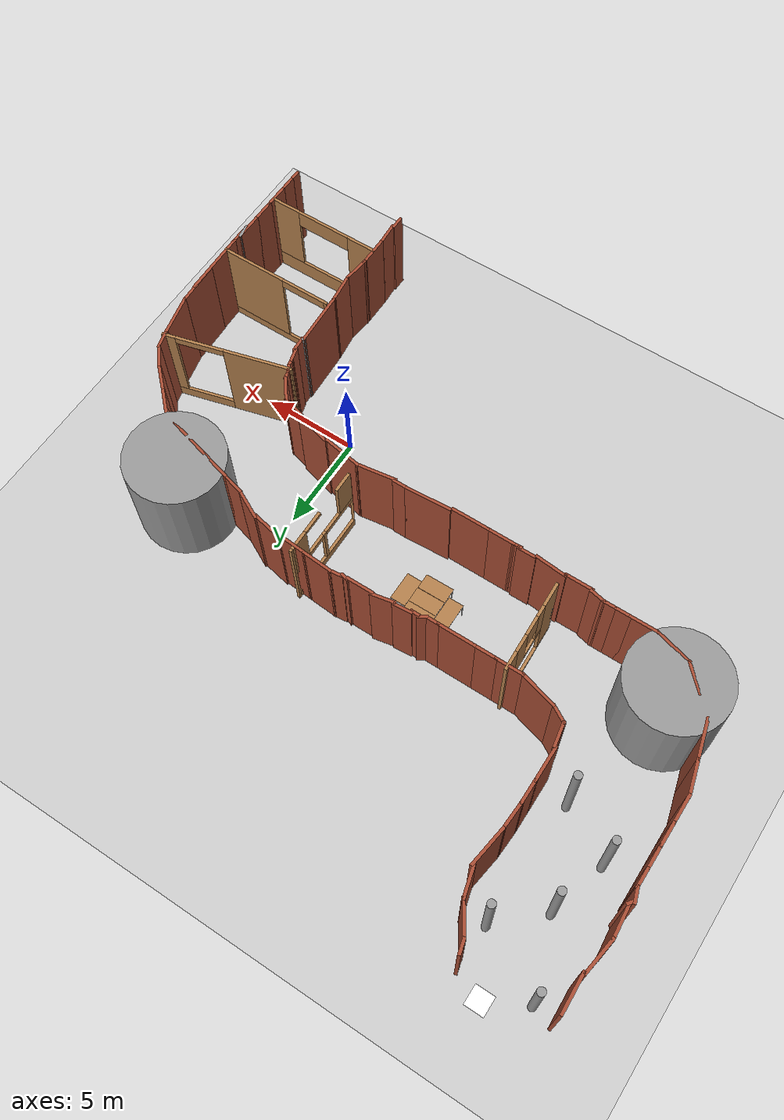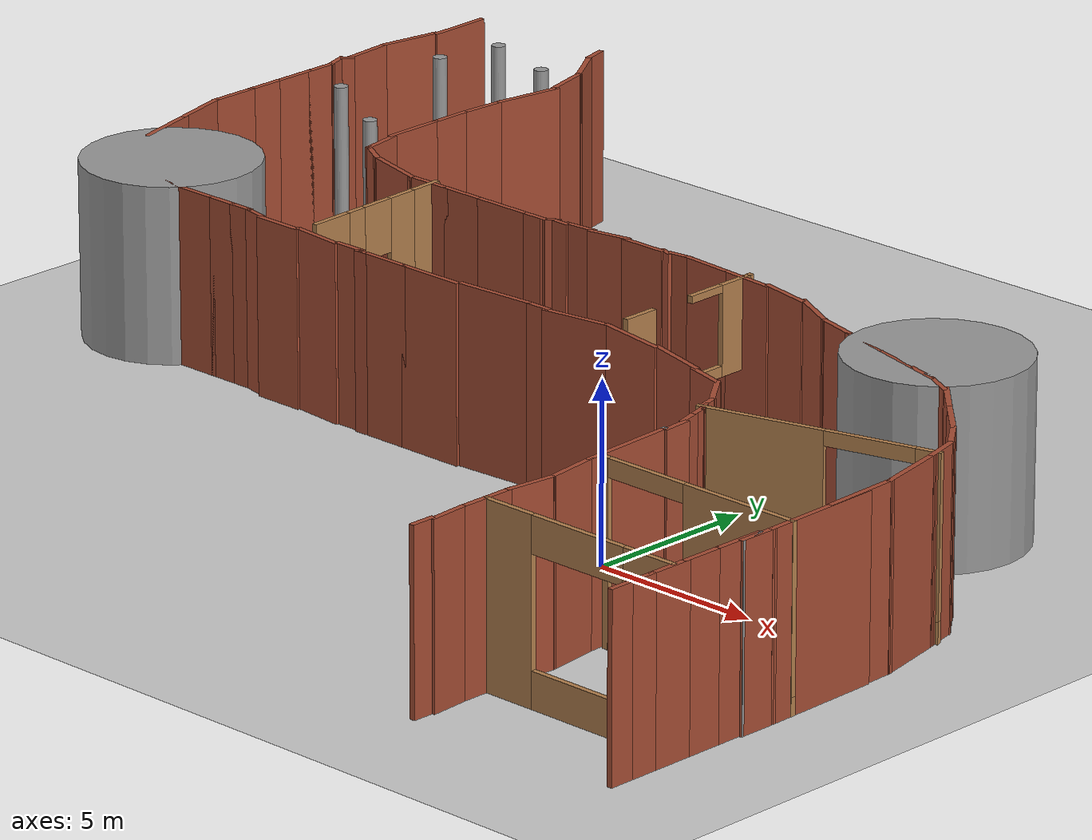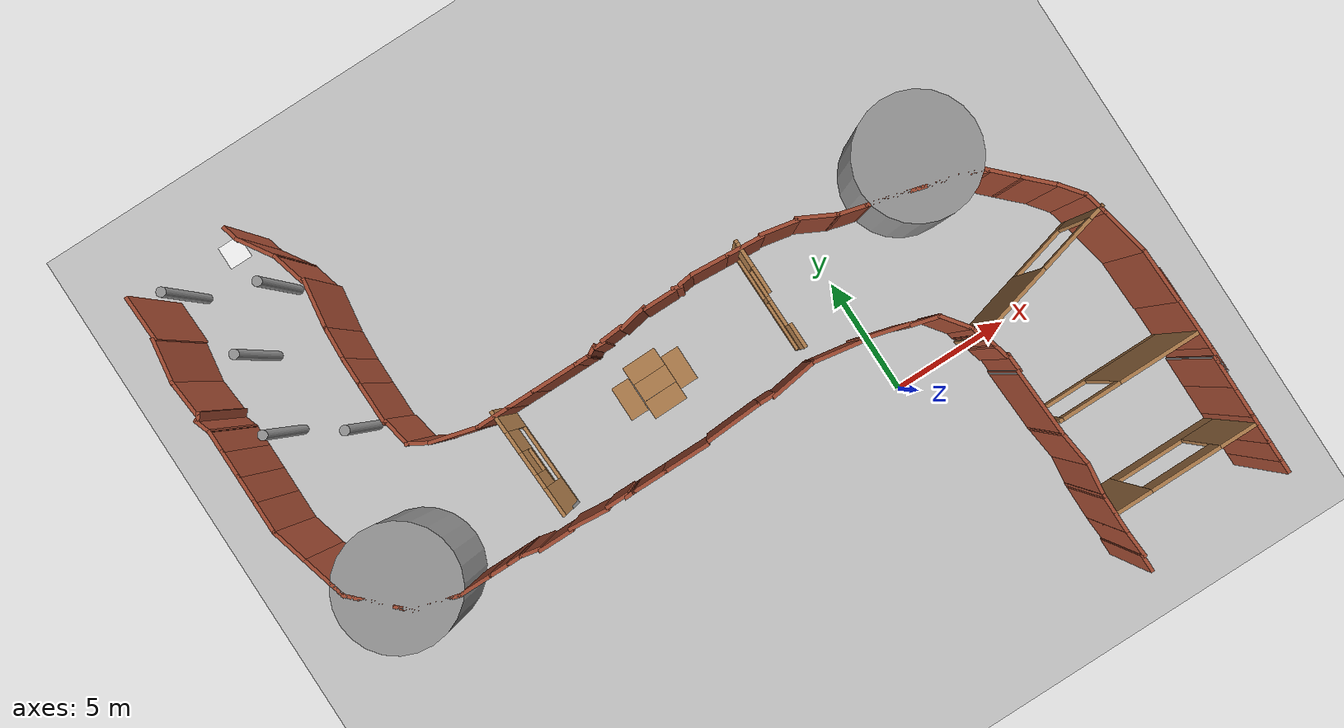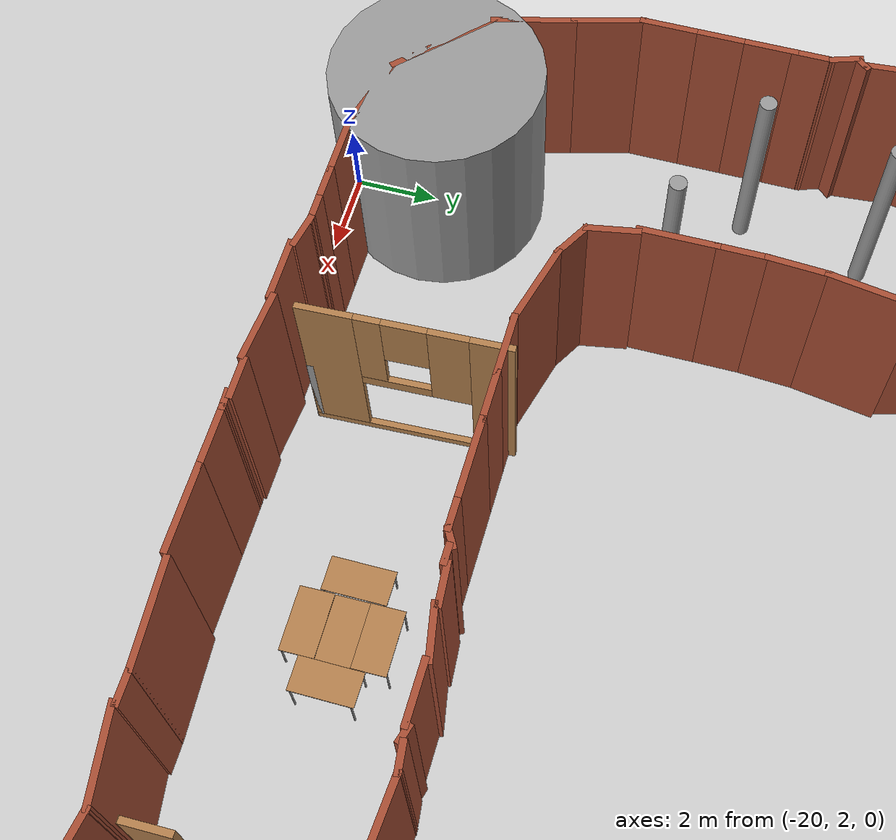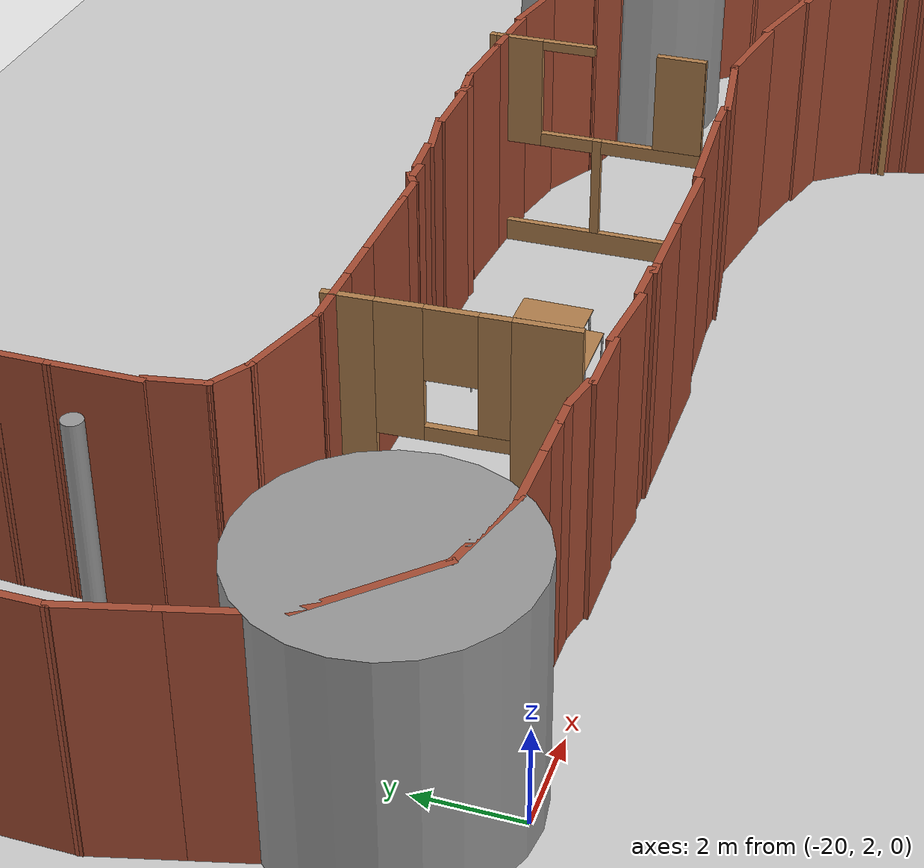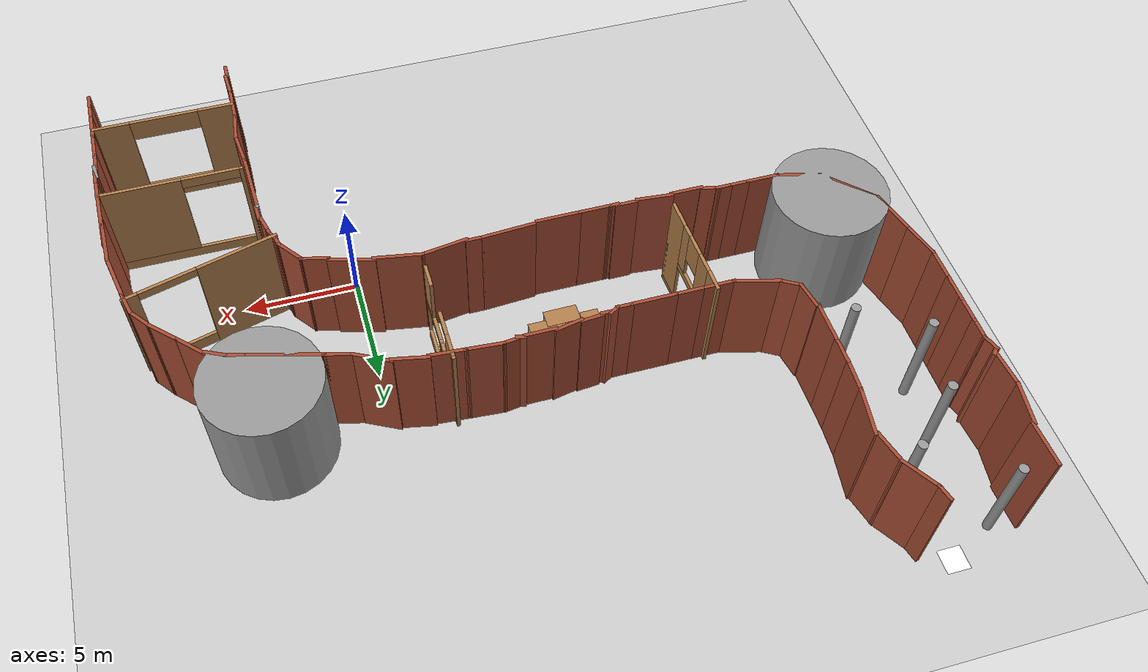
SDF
<sdf version="1.6">
 <world name="default">
  <light name="sun" type="directional">
   <pose>0 0 10 0 -0 0</pose>
   <diffuse>0.8 0.8 0.8 1</diffuse>
   <specular>0.2 0.2 0.2 1</specular>
   <attenuation>
    <range>1000</range>
    <constant>0.9</constant>
    <linear>0.01</linear>
    <quadratic>0.001</quadratic>
   </attenuation>
   <direction>-0.5 0.1 -0.9</direction>
  </light>
  <model name="ground_plane">
   <static>1</static>
   <link name="link">
    <collision name="collision">
     <geometry><plane><normal>0 0 1</normal><size>100 100</size></plane></geometry>
     <surface><friction><ode><mu>100</mu><mu2>50</mu2></ode></friction></surface>
    </collision>
    <visual name="visual">
     <cast_shadows>0</cast_shadows>
     <geometry><plane><normal>0 0 1</normal><size>100 100</size></plane></geometry>
     <material>
      <script><uri>file://media/materials/scripts/gazebo.material</uri><name>Gazebo/Grey</name></script>
     </material>
    </visual>
   </link>
  </model>
  <gravity>0 0 -9.8</gravity>
  <magnetic_field>6e-06 2.3e-05 -4.2e-05</magnetic_field>
  <atmosphere type="adiabatic"/>
  <physics name="default_physics" default="0" type="ode">
   <max_step_size>0.001</max_step_size>
   <real_time_factor>1</real_time_factor>
   <real_time_update_rate>1000</real_time_update_rate>
  </physics>
  <scene><ambient>0.4 0.4 0.4 1</ambient><background>0.7 0.7 0.7 1</background><shadows>1</shadows></scene>
  <spherical_coordinates>
   <surface_model>EARTH_WGS84</surface_model>
   <latitude_deg>0</latitude_deg>
   <longitude_deg>0</longitude_deg>
   <elevation>0</elevation>
   <heading_deg>0</heading_deg>
  </spherical_coordinates>
  <model name="testing_world3">
   <pose>-6.53172 4.3084 0 0 -0 0</pose>
   <link name="Wall_10">
    <collision name="Wall_10_Collision">
     <geometry><box><size>2.30782 0.15 5</size></box></geometry>
     <pose>0 0 2.5 0 -0 0</pose>
    </collision>
    <visual name="Wall_10_Visual">
     <pose>0 0 2.5 0 -0 0</pose>
     <geometry><box><size>2.30782 0.15 5</size></box></geometry>
     <material>
      <script><uri>file://media/materials/scripts/gazebo.material</uri><name>Gazebo/Bricks</name></script>
      <ambient>1 1 1 1</ambient>
     </material>
     <meta><layer>0</layer></meta>
    </visual>
    <pose>16.3496 -5.59332 0 0 -0 1.60372</pose>
   </link>
   <link name="Wall_100">
    <collision name="Wall_100_Collision">
     <geometry><box><size>0.5 0.15 5</size></box></geometry>
     <pose>0 0 2.5 0 -0 0</pose>
    </collision>
    <visual name="Wall_100_Visual">
     <pose>0 0 2.5 0 -0 0</pose>
     <geometry><box><size>0.5 0.15 5</size></box></geometry>
     <material>
      <script><uri>file://media/materials/scripts/gazebo.material</uri><name>Gazebo/Bricks</name></script>
      <ambient>1 1 1 1</ambient>
     </material>
     <meta><layer>0</layer></meta>
    </visual>
    <pose>9.6284 -3.94444 0 0 -0 -1.0472</pose>
   </link>
   <link name="Wall_101">
    <collision name="Wall_101_Collision">
     <geometry><box><size>0.5 0.15 5</size></box></geometry>
     <pose>0 0 2.5 0 -0 0</pose>
    </collision>
    <visual name="Wall_101_Visual">
     <pose>0 0 2.5 0 -0 0</pose>
     <geometry><box><size>0.5 0.15 5</size></box></geometry>
     <material>
      <script><uri>file://media/materials/scripts/gazebo.material</uri><name>Gazebo/Bricks</name></script>
      <ambient>1 1 1 1</ambient>
     </material>
     <meta><layer>0</layer></meta>
    </visual>
    <pose>9.76119 -4.26503 0 0 -0 -1.309</pose>
   </link>
   <link name="Wall_102">
    <collision name="Wall_102_Collision">
     <geometry><box><size>0.761275 0.15 5</size></box></geometry>
     <pose>0 0 2.5 0 -0 0</pose>
    </collision>
    <visual name="Wall_102_Visual">
     <pose>0 0 2.5 0 -0 0</pose>
     <geometry><box><size>0.761275 0.15 5</size></box></geometry>
     <material>
      <script><uri>file://media/materials/scripts/gazebo.material</uri><name>Gazebo/Bricks</name></script>
      <ambient>1 1 1 1</ambient>
     </material>
     <meta><layer>0</layer></meta>
    </visual>
    <pose>9.88573 -4.72926 0 0 -0 -1.30853</pose>
   </link>
   <link name="Wall_103">
    <collision name="Wall_103_Collision">
     <geometry><box><size>0.863527 0.15 5</size></box></geometry>
     <pose>0 0 2.5 0 -0 0</pose>
    </collision>
    <visual name="Wall_103_Visual">
     <pose>0 0 2.5 0 -0 0</pose>
     <geometry><box><size>0.863527 0.15 5</size></box></geometry>
     <material>
      <script><uri>file://media/materials/scripts/gazebo.material</uri><name>Gazebo/Bricks</name></script>
      <ambient>1 1 1 1</ambient>
     </material>
     <meta><layer>0</layer></meta>
    </visual>
    <pose>10.0573 -5.38055 0 0 -0 -1.5102</pose>
   </link>
   <link name="Wall_104">
    <collision name="Wall_104_Collision">
     <geometry><box><size>0.15 0.15 5</size></box></geometry>
     <pose>0 0 2.5 0 -0 0</pose>
    </collision>
    <visual name="Wall_104_Visual">
     <pose>0 0 2.5 0 -0 0</pose>
     <geometry><box><size>0.15 0.15 5</size></box></geometry>
     <material>
      <script><uri>file://media/materials/scripts/gazebo.material</uri><name>Gazebo/Grey</name></script>
      <ambient>1 1 1 1</ambient>
     </material>
     <meta><layer>0</layer></meta>
    </visual>
    <pose>10.0082 -5.73666 0 0 -0 0</pose>
   </link>
   <link name="Wall_11">
    <collision name="Wall_11_Collision">
     <geometry><box><size>2.18167 0.15 5</size></box></geometry>
     <pose>0 0 2.5 0 -0 0</pose>
    </collision>
    <visual name="Wall_11_Visual">
     <pose>0 0 2.5 0 -0 0</pose>
     <geometry><box><size>2.18167 0.15 5</size></box></geometry>
     <material>
      <script><uri>file://media/materials/scripts/gazebo.material</uri><name>Gazebo/Bricks</name></script>
      <ambient>1 1 1 1</ambient>
     </material>
     <meta><layer>0</layer></meta>
    </visual>
    <pose>16.1021 -3.52182 0 0 -0 1.78103</pose>
   </link>
   <link name="Wall_12">
    <collision name="Wall_12_Collision">
     <geometry><box><size>1.11413 0.15 5</size></box></geometry>
     <pose>0 0 2.5 0 -0 0</pose>
    </collision>
    <visual name="Wall_12_Visual">
     <pose>0 0 2.5 0 -0 0</pose>
     <geometry><box><size>1.11413 0.15 5</size></box></geometry>
     <material>
      <script><uri>file://media/materials/scripts/gazebo.material</uri><name>Gazebo/Bricks</name></script>
      <ambient>1 1 1 1</ambient>
     </material>
     <meta><layer>0</layer></meta>
    </visual>
    <pose>15.7686 -2.06182 0 0 -0 1.82559</pose>
   </link>
   <link name="Wall_13">
    <collision name="Wall_13_Collision">
     <geometry><box><size>1.22947 0.15 5</size></box></geometry>
     <pose>0 0 2.5 0 -0 0</pose>
    </collision>
    <visual name="Wall_13_Visual">
     <pose>0 0 2.5 0 -0 0</pose>
     <geometry><box><size>1.22947 0.15 5</size></box></geometry>
     <material>
      <script><uri>file://media/materials/scripts/gazebo.material</uri><name>Gazebo/Bricks</name></script>
      <ambient>1 1 1 1</ambient>
     </material>
     <meta><layer>0</layer></meta>
    </visual>
    <pose>15.3141 -1.17032 0 0 -0 2.23541</pose>
   </link>
   <link name="Wall_14">
    <collision name="Wall_14_Collision">
     <geometry><box><size>1.50994 0.15 5</size></box></geometry>
     <pose>0 0 2.5 0 -0 0</pose>
    </collision>
    <visual name="Wall_14_Visual">
     <pose>0 0 2.5 0 -0 0</pose>
     <geometry><box><size>1.50994 0.15 5</size></box></geometry>
     <material>
      <script><uri>file://media/materials/scripts/gazebo.material</uri><name>Gazebo/Bricks</name></script>
      <ambient>1 1 1 1</ambient>
     </material>
     <meta><layer>0</layer></meta>
    </visual>
    <pose>14.4961 -0.268745 0 0 -0 2.36497</pose>
   </link>
   <link name="Wall_15">
    <collision name="Wall_15_Collision">
     <geometry><box><size>1.5 0.15 5</size></box></geometry>
     <pose>0 0 2.5 0 -0 0</pose>
    </collision>
    <visual name="Wall_15_Visual">
     <pose>0 0 2.5 0 -0 0</pose>
     <geometry><box><size>1.5 0.15 5</size></box></geometry>
     <material>
      <script><uri>file://media/materials/scripts/gazebo.material</uri><name>Gazebo/Bricks</name></script>
      <ambient>1 1 1 1</ambient>
     </material>
     <meta><layer>0</layer></meta>
    </visual>
    <pose>13.5338 0.685124 0 0 -0 2.35619</pose>
   </link>
   <link name="Wall_16">
    <collision name="Wall_16_Collision">
     <geometry><box><size>0.982832 0.15 5</size></box></geometry>
     <pose>0 0 2.5 0 -0 0</pose>
    </collision>
    <visual name="Wall_16_Visual">
     <pose>0 0 2.5 0 -0 0</pose>
     <geometry><box><size>0.982832 0.15 5</size></box></geometry>
     <material>
      <script><uri>file://media/materials/scripts/gazebo.material</uri><name>Gazebo/Bricks</name></script>
      <ambient>1 1 1 1</ambient>
     </material>
     <meta><layer>0</layer></meta>
    </visual>
    <pose>12.6814 1.27242 0 0 -0 2.69258</pose>
   </link>
   <link name="Wall_17">
    <collision name="Wall_17_Collision">
     <geometry><box><size>1 0.15 5</size></box></geometry>
     <pose>0 0 2.5 0 -0 0</pose>
    </collision>
    <visual name="Wall_17_Visual">
     <pose>0 0 2.5 0 -0 0</pose>
     <geometry><box><size>1 0.15 5</size></box></geometry>
     <material>
      <script><uri>file://media/materials/scripts/gazebo.material</uri><name>Gazebo/Bricks</name></script>
      <ambient>1 1 1 1</ambient>
     </material>
     <meta><layer>0</layer></meta>
    </visual>
    <pose>11.8957 1.56317 0 0 -0 2.87979</pose>
   </link>
   <link name="Wall_18">
    <collision name="Wall_18_Collision">
     <geometry><box><size>1.5 0.15 5</size></box></geometry>
     <pose>0 0 2.5 0 -0 0</pose>
    </collision>
    <visual name="Wall_18_Visual">
     <pose>0 0 2.5 0 -0 0</pose>
     <geometry><box><size>1.5 0.15 5</size></box></geometry>
     <material>
      <script><uri>file://media/materials/scripts/gazebo.material</uri><name>Gazebo/Bricks</name></script>
      <ambient>1 1 1 1</ambient>
     </material>
     <meta><layer>0</layer></meta>
    </visual>
    <pose>10.8332 1.84787 0 0 -0 2.87979</pose>
   </link>
   <link name="Wall_19">
    <collision name="Wall_19_Collision">
     <geometry><box><size>1.75 0.15 5</size></box></geometry>
     <pose>0 0 2.5 0 -0 0</pose>
    </collision>
    <visual name="Wall_19_Visual">
     <pose>0 0 2.5 0 -0 0</pose>
     <geometry><box><size>1.75 0.15 5</size></box></geometry>
     <material>
      <script><uri>file://media/materials/scripts/gazebo.material</uri><name>Gazebo/Bricks</name></script>
      <ambient>1 1 1 1</ambient>
     </material>
     <meta><layer>0</layer></meta>
    </visual>
    <pose>9.40845 2.22963 0 0 -0 2.87979</pose>
   </link>
   <link name="Wall_20">
    <collision name="Wall_20_Collision">
     <geometry><box><size>1.25 0.15 5</size></box></geometry>
     <pose>0 0 2.5 0 -0 0</pose>
    </collision>
    <visual name="Wall_20_Visual">
     <pose>0 0 2.5 0 -0 0</pose>
     <geometry><box><size>1.25 0.15 5</size></box></geometry>
     <material>
      <script><uri>file://media/materials/scripts/gazebo.material</uri><name>Gazebo/Bricks</name></script>
      <ambient>1 1 1 1</ambient>
     </material>
     <meta><layer>0</layer></meta>
    </visual>
    <pose>8.10445 2.57904 0 0 -0 2.87979</pose>
   </link>
   <link name="Wall_21">
    <collision name="Wall_21_Collision">
     <geometry><box><size>1.69416 0.15 5</size></box></geometry>
     <pose>0 0 2.5 0 -0 0</pose>
    </collision>
    <visual name="Wall_21_Visual">
     <pose>0 0 2.5 0 -0 0</pose>
     <geometry><box><size>1.69416 0.15 5</size></box></geometry>
     <material>
      <script><uri>file://media/materials/scripts/gazebo.material</uri><name>Gazebo/Bricks</name></script>
      <ambient>1 1 1 1</ambient>
     </material>
     <meta><layer>0</layer></meta>
    </visual>
    <pose>6.88581 3.07298 0 0 -0 2.66879</pose>
   </link>
   <link name="Wall_22">
    <collision name="Wall_22_Collision">
     <geometry><box><size>1.59867 0.15 5</size></box></geometry>
     <pose>0 0 2.5 0 -0 0</pose>
    </collision>
    <visual name="Wall_22_Visual">
     <pose>0 0 2.5 0 -0 0</pose>
     <geometry><box><size>1.59867 0.15 5</size></box></geometry>
     <material>
      <script><uri>file://media/materials/scripts/gazebo.material</uri><name>Gazebo/Bricks</name></script>
      <ambient>1 1 1 1</ambient>
     </material>
     <meta><layer>0</layer></meta>
    </visual>
    <pose>5.48805 3.49534 0 0 -0 2.94496</pose>
   </link>
   <link name="Wall_23">
    <collision name="Wall_23_Collision">
     <geometry><box><size>1.61128 0.15 5</size></box></geometry>
     <pose>0 0 2.5 0 -0 0</pose>
    </collision>
    <visual name="Wall_23_Visual">
     <pose>0 0 2.5 0 -0 0</pose>
     <geometry><box><size>1.61128 0.15 5</size></box></geometry>
     <material>
      <script><uri>file://media/materials/scripts/gazebo.material</uri><name>Gazebo/Bricks</name></script>
      <ambient>1 1 1 1</ambient>
     </material>
     <meta><layer>0</layer></meta>
    </visual>
    <pose>4.04895 3.61896 0 0 -0 3.06917</pose>
   </link>
   <link name="Wall_24">
    <collision name="Wall_24_Collision">
     <geometry><box><size>1.64283 0.15 5</size></box></geometry>
     <pose>0 0 2.5 0 -0 0</pose>
    </collision>
    <visual name="Wall_24_Visual">
     <pose>0 0 2.5 0 -0 0</pose>
     <geometry><box><size>1.64283 0.15 5</size></box></geometry>
     <material>
      <script><uri>file://media/materials/scripts/gazebo.material</uri><name>Gazebo/Bricks</name></script>
      <ambient>1 1 1 1</ambient>
     </material>
     <meta><layer>0</layer></meta>
    </visual>
    <pose>2.5757 3.72496 0 0 -0 3.07036</pose>
   </link>
   <link name="Wall_25">
    <collision name="Wall_25_Collision">
     <geometry><box><size>0.720151 0.15 5</size></box></geometry>
     <pose>0 0 2.5 0 -0 0</pose>
    </collision>
    <visual name="Wall_25_Visual">
     <pose>0 0 2.5 0 -0 0</pose>
     <geometry><box><size>0.720151 0.15 5</size></box></geometry>
     <material>
      <script><uri>file://media/materials/scripts/gazebo.material</uri><name>Gazebo/Bricks</name></script>
      <ambient>1 1 1 1</ambient>
     </material>
     <meta><layer>0</layer></meta>
    </visual>
    <pose>1.54829 3.74285 0 0 -0 -3.01766</pose>
   </link>
   <link name="Wall_26">
    <collision name="Wall_26_Collision">
     <geometry><box><size>0.458341 0.15 5</size></box></geometry>
     <pose>0 0 2.5 0 -0 0</pose>
    </collision>
    <visual name="Wall_26_Visual">
     <pose>0 0 2.5 0 -0 0</pose>
     <geometry><box><size>0.458341 0.15 5</size></box></geometry>
     <material>
      <script><uri>file://media/materials/scripts/gazebo.material</uri><name>Gazebo/Bricks</name></script>
      <ambient>1 1 1 1</ambient>
     </material>
     <meta><layer>0</layer></meta>
    </visual>
    <pose>1.11714 3.67912 0 0 -0 2.86388</pose>
   </link>
   <link name="Wall_27">
    <collision name="Wall_27_Collision">
     <geometry><box><size>1.42924 0.15 5</size></box></geometry>
     <pose>0 0 2.5 0 -0 0</pose>
    </collision>
    <visual name="Wall_27_Visual">
     <pose>0 0 2.5 0 -0 0</pose>
     <geometry><box><size>1.42924 0.15 5</size></box></geometry>
     <material>
      <script><uri>file://media/materials/scripts/gazebo.material</uri><name>Gazebo/Bricks</name></script>
      <ambient>1 1 1 1</ambient>
     </material>
     <meta><layer>0</layer></meta>
    </visual>
    <pose>0.329252 3.65063 0 0 -0 3.14159</pose>
   </link>
   <link name="Wall_28">
    <collision name="Wall_28_Collision">
     <geometry><box><size>1.27029 0.15 5</size></box></geometry>
     <pose>0 0 2.5 0 -0 0</pose>
    </collision>
    <visual name="Wall_28_Visual">
     <pose>0 0 2.5 0 -0 0</pose>
     <geometry><box><size>1.27029 0.15 5</size></box></geometry>
     <material>
      <script><uri>file://media/materials/scripts/gazebo.material</uri><name>Gazebo/Bricks</name></script>
      <ambient>1 1 1 1</ambient>
     </material>
     <meta><layer>0</layer></meta>
    </visual>
    <pose>-0.860369 3.61525 0 0 -0 -2.95096</pose>
   </link>
   <link name="Wall_29">
    <collision name="Wall_29_Collision">
     <geometry><box><size>1.00294 0.15 5</size></box></geometry>
     <pose>0 0 2.5 0 -0 0</pose>
    </collision>
    <visual name="Wall_29_Visual">
     <pose>0 0 2.5 0 -0 0</pose>
     <geometry><box><size>1.00294 0.15 5</size></box></geometry>
     <material>
      <script><uri>file://media/materials/scripts/gazebo.material</uri><name>Gazebo/Bricks</name></script>
      <ambient>1 1 1 1</ambient>
     </material>
     <meta><layer>0</layer></meta>
    </visual>
    <pose>-1.83537 3.54449 0 0 -0 -3.05854</pose>
   </link>
   <link name="Wall_3">
    <collision name="Wall_3_Collision">
     <geometry><box><size>1.5 0.15 5</size></box></geometry>
     <pose>0 0 2.5 0 -0 0</pose>
    </collision>
    <visual name="Wall_3_Visual">
     <pose>0 0 2.5 0 -0 0</pose>
     <geometry><box><size>1.5 0.15 5</size></box></geometry>
     <material>
      <script><uri>file://media/materials/scripts/gazebo.material</uri><name>Gazebo/Bricks</name></script>
      <ambient>1 1 1 1</ambient>
     </material>
     <meta><layer>0</layer></meta>
    </visual>
    <pose>16.3851 -9.88032 0 0 -0 1.5708</pose>
   </link>
   <link name="Wall_30">
    <collision name="Wall_30_Collision">
     <geometry><box><size>0.5 0.15 5</size></box></geometry>
     <pose>0 0 2.5 0 -0 0</pose>
    </collision>
    <visual name="Wall_30_Visual">
     <pose>0 0 2.5 0 -0 0</pose>
     <geometry><box><size>0.5 0.15 5</size></box></geometry>
     <material>
      <script><uri>file://media/materials/scripts/gazebo.material</uri><name>Gazebo/Bricks</name></script>
      <ambient>1 1 1 1</ambient>
     </material>
     <meta><layer>0</layer></meta>
    </visual>
    <pose>-2.43537 3.43836 0 0 -0 3.14159</pose>
   </link>
   <link name="Wall_31">
    <collision name="Wall_31_Collision">
     <geometry><box><size>0.539009 0.15 5</size></box></geometry>
     <pose>0 0 2.5 0 -0 0</pose>
    </collision>
    <visual name="Wall_31_Visual">
     <pose>0 0 2.5 0 -0 0</pose>
     <geometry><box><size>0.539009 0.15 5</size></box></geometry>
     <material>
      <script><uri>file://media/materials/scripts/gazebo.material</uri><name>Gazebo/Bricks</name></script>
      <ambient>1 1 1 1</ambient>
     </material>
     <meta><layer>0</layer></meta>
    </visual>
    <pose>-2.77941 3.41289 0 0 -0 -2.62411</pose>
   </link>
   <link name="Wall_32">
    <collision name="Wall_32_Collision">
     <geometry><box><size>0.75 0.15 5</size></box></geometry>
     <pose>0 0 2.5 0 -0 0</pose>
    </collision>
    <visual name="Wall_32_Visual">
     <pose>0 0 2.5 0 -0 0</pose>
     <geometry><box><size>0.75 0.15 5</size></box></geometry>
     <material>
      <script><uri>file://media/materials/scripts/gazebo.material</uri><name>Gazebo/Bricks</name></script>
      <ambient>1 1 1 1</ambient>
     </material>
     <meta><layer>0</layer></meta>
    </visual>
    <pose>-3.24844 3.31667 0 0 -0 3.14159</pose>
   </link>
   <link name="Wall_34">
    <collision name="Wall_34_Collision">
     <geometry><box><size>2 0.15 5</size></box></geometry>
     <pose>0 0 2.5 0 -0 0</pose>
    </collision>
    <visual name="Wall_34_Visual">
     <pose>0 0 2.5 0 -0 0</pose>
     <geometry><box><size>2 0.15 5</size></box></geometry>
     <material>
      <script><uri>file://media/materials/scripts/gazebo.material</uri><name>Gazebo/Bricks</name></script>
      <ambient>1 1 1 1</ambient>
     </material>
     <meta><layer>0</layer></meta>
    </visual>
    <pose>-4.47344 3.31667 0 0 -0 3.14159</pose>
   </link>
   <link name="Wall_35">
    <collision name="Wall_35_Collision">
     <geometry><box><size>1.25 0.15 5</size></box></geometry>
     <pose>0 0 2.5 0 -0 0</pose>
    </collision>
    <visual name="Wall_35_Visual">
     <pose>0 0 2.5 0 -0 0</pose>
     <geometry><box><size>1.25 0.15 5</size></box></geometry>
     <material>
      <script><uri>file://media/materials/scripts/gazebo.material</uri><name>Gazebo/Bricks</name></script>
      <ambient>1 1 1 1</ambient>
     </material>
     <meta><layer>0</layer></meta>
    </visual>
    <pose>-5.94844 3.31667 0 0 -0 3.14159</pose>
   </link>
   <link name="Wall_36">
    <collision name="Wall_36_Collision">
     <geometry><box><size>1.5 0.15 5</size></box></geometry>
     <pose>0 0 2.5 0 -0 0</pose>
    </collision>
    <visual name="Wall_36_Visual">
     <pose>0 0 2.5 0 -0 0</pose>
     <geometry><box><size>1.5 0.15 5</size></box></geometry>
     <material>
      <script><uri>file://media/materials/scripts/gazebo.material</uri><name>Gazebo/Bricks</name></script>
      <ambient>1 1 1 1</ambient>
     </material>
     <meta><layer>0</layer></meta>
    </visual>
    <pose>-7.17344 3.31667 0 0 -0 3.14159</pose>
   </link>
   <link name="Wall_37">
    <collision name="Wall_37_Collision">
     <geometry><box><size>2 0.15 5</size></box></geometry>
     <pose>0 0 2.5 0 -0 0</pose>
    </collision>
    <visual name="Wall_37_Visual">
     <pose>0 0 2.5 0 -0 0</pose>
     <geometry><box><size>2 0.15 5</size></box></geometry>
     <material>
      <script><uri>file://media/materials/scripts/gazebo.material</uri><name>Gazebo/Bricks</name></script>
      <ambient>1 1 1 1</ambient>
     </material>
     <meta><layer>0</layer></meta>
    </visual>
    <pose>-8.74193 3.55608 0 0 -0 2.87979</pose>
   </link>
   <link name="Wall_38">
    <collision name="Wall_38_Collision">
     <geometry><box><size>1 0.15 5</size></box></geometry>
     <pose>0 0 2.5 0 -0 0</pose>
    </collision>
    <visual name="Wall_38_Visual">
     <pose>0 0 2.5 0 -0 0</pose>
     <geometry><box><size>1 0.15 5</size></box></geometry>
     <material>
      <script><uri>file://media/materials/scripts/gazebo.material</uri><name>Gazebo/Bricks</name></script>
      <ambient>1 1 1 1</ambient>
     </material>
     <meta><layer>0</layer></meta>
    </visual>
    <pose>-10.0035 4.00799 0 0 -0 2.61799</pose>
   </link>
   <link name="Wall_39">
    <collision name="Wall_39_Collision">
     <geometry><box><size>1.2616 0.15 5</size></box></geometry>
     <pose>0 0 2.5 0 -0 0</pose>
    </collision>
    <visual name="Wall_39_Visual">
     <pose>0 0 2.5 0 -0 0</pose>
     <geometry><box><size>1.2616 0.15 5</size></box></geometry>
     <material>
      <script><uri>file://media/materials/scripts/gazebo.material</uri><name>Gazebo/Bricks</name></script>
      <ambient>1 1 1 1</ambient>
     </material>
     <meta><layer>0</layer></meta>
    </visual>
    <pose>-10.4696 4.76756 0 0 -0 1.74824</pose>
   </link>
   <link name="Wall_4">
    <collision name="Wall_4_Collision">
     <geometry><box><size>0.784982 0.15 5</size></box></geometry>
     <pose>0 0 2.5 0 -0 0</pose>
    </collision>
    <visual name="Wall_4_Visual">
     <pose>0 0 2.5 0 -0 0</pose>
     <geometry><box><size>0.784982 0.15 5</size></box></geometry>
     <material>
      <script><uri>file://media/materials/scripts/gazebo.material</uri><name>Gazebo/Grey</name></script>
      <ambient>1 1 1 1</ambient>
     </material>
     <meta><layer>0</layer></meta>
    </visual>
    <pose>16.4206 -9.52082 0 0 -0 -1.45875</pose>
   </link>
   <link name="Wall_40">
    <collision name="Wall_40_Collision">
     <geometry><box><size>1.84697 0.15 5</size></box></geometry>
     <pose>0 0 2.5 0 -0 0</pose>
    </collision>
    <visual name="Wall_40_Visual">
     <pose>0 0 2.5 0 -0 0</pose>
     <geometry><box><size>1.84697 0.15 5</size></box></geometry>
     <material>
      <script><uri>file://media/materials/scripts/gazebo.material</uri><name>Gazebo/Bricks</name></script>
      <ambient>1 1 1 1</ambient>
     </material>
     <meta><layer>0</layer></meta>
    </visual>
    <pose>-10.6452 6.16309 0 0 -0 1.57866</pose>
   </link>
   <link name="Wall_41">
    <collision name="Wall_41_Collision">
     <geometry><box><size>1.25 0.15 5</size></box></geometry>
     <pose>0 0 2.5 0 -0 0</pose>
    </collision>
    <visual name="Wall_41_Visual">
     <pose>0 0 2.5 0 -0 0</pose>
     <geometry><box><size>1.25 0.15 5</size></box></geometry>
     <material>
      <script><uri>file://media/materials/scripts/gazebo.material</uri><name>Gazebo/Bricks</name></script>
      <ambient>1 1 1 1</ambient>
     </material>
     <meta><layer>0</layer></meta>
    </visual>
    <pose>-10.6518 7.56155 0 0 -0 1.5708</pose>
   </link>
   <link name="Wall_42">
    <collision name="Wall_42_Collision">
     <geometry><box><size>1.45529 0.15 5</size></box></geometry>
     <pose>0 0 2.5 0 -0 0</pose>
    </collision>
    <visual name="Wall_42_Visual">
     <pose>0 0 2.5 0 -0 0</pose>
     <geometry><box><size>1.45529 0.15 5</size></box></geometry>
     <material>
      <script><uri>file://media/materials/scripts/gazebo.material</uri><name>Gazebo/Bricks</name></script>
      <ambient>1 1 1 1</ambient>
     </material>
     <meta><layer>0</layer></meta>
    </visual>
    <pose>-10.6167 8.76324 0 0 -0 1.51689</pose>
   </link>
   <link name="Wall_43">
    <collision name="Wall_43_Collision">
     <geometry><box><size>2.0915 0.15 5</size></box></geometry>
     <pose>0 0 2.5 0 -0 0</pose>
    </collision>
    <visual name="Wall_43_Visual">
     <pose>0 0 2.5 0 -0 0</pose>
     <geometry><box><size>2.0915 0.15 5</size></box></geometry>
     <material>
      <script><uri>file://media/materials/scripts/gazebo.material</uri><name>Gazebo/Bricks</name></script>
      <ambient>1 1 1 1</ambient>
     </material>
     <meta><layer>0</layer></meta>
    </visual>
    <pose>-10.44 10.3753 0 0 -0 1.4245</pose>
   </link>
   <link name="Wall_44">
    <collision name="Wall_44_Collision">
     <geometry><box><size>1.5 0.15 5</size></box></geometry>
     <pose>0 0 2.5 0 -0 0</pose>
    </collision>
    <visual name="Wall_44_Visual">
     <pose>0 0 2.5 0 -0 0</pose>
     <geometry><box><size>1.5 0.15 5</size></box></geometry>
     <material>
      <script><uri>file://media/materials/scripts/gazebo.material</uri><name>Gazebo/Bricks</name></script>
      <ambient>1 1 1 1</ambient>
     </material>
     <meta><layer>0</layer></meta>
    </visual>
    <pose>-10.544 11.9877 0 0 -0 1.8326</pose>
   </link>
   <link name="Wall_45">
    <collision name="Wall_45_Collision">
     <geometry><box><size>1.69608 0.15 5</size></box></geometry>
     <pose>0 0 2.5 0 -0 0</pose>
    </collision>
    <visual name="Wall_45_Visual">
     <pose>0 0 2.5 0 -0 0</pose>
     <geometry><box><size>1.69608 0.15 5</size></box></geometry>
     <material>
      <script><uri>file://media/materials/scripts/gazebo.material</uri><name>Gazebo/Bricks</name></script>
      <ambient>1 1 1 1</ambient>
     </material>
     <meta><layer>0</layer></meta>
    </visual>
    <pose>-11.1371 13.2897 0 0 -0 2.14284</pose>
   </link>
   <link name="Wall_46">
    <collision name="Wall_46_Collision">
     <geometry><box><size>0.75 0.15 5</size></box></geometry>
     <pose>0 0 2.5 0 -0 0</pose>
    </collision>
    <visual name="Wall_46_Visual">
     <pose>0 0 2.5 0 -0 0</pose>
     <geometry><box><size>0.75 0.15 5</size></box></geometry>
     <material>
      <script><uri>file://media/materials/scripts/gazebo.material</uri><name>Gazebo/Bricks</name></script>
      <ambient>1 1 1 1</ambient>
     </material>
     <meta><layer>0</layer></meta>
    </visual>
    <pose>-11.6333 14.2294 0 0 -0 1.8326</pose>
   </link>
   <link name="Wall_48">
    <collision name="Wall_48_Collision">
     <geometry><box><size>1.44172 0.15 5</size></box></geometry>
     <pose>0 0 2.5 0 -0 0</pose>
    </collision>
    <visual name="Wall_48_Visual">
     <pose>0 0 2.5 0 -0 0</pose>
     <geometry><box><size>1.44172 0.15 5</size></box></geometry>
     <material>
      <script><uri>file://media/materials/scripts/gazebo.material</uri><name>Gazebo/Bricks</name></script>
      <ambient>1 1 1 1</ambient>
     </material>
     <meta><layer>0</layer></meta>
    </visual>
    <pose>10.2582 -10.6601 0 0 -0 1.46102</pose>
   </link>
   <link name="Wall_49">
    <collision name="Wall_49_Collision">
     <geometry><box><size>1.59268 0.15 5</size></box></geometry>
     <pose>0 0 2.5 0 -0 0</pose>
    </collision>
    <visual name="Wall_49_Visual">
     <pose>0 0 2.5 0 -0 0</pose>
     <geometry><box><size>1.59268 0.15 5</size></box></geometry>
     <material>
      <script><uri>file://media/materials/scripts/gazebo.material</uri><name>Gazebo/Bricks</name></script>
      <ambient>1 1 1 1</ambient>
     </material>
     <meta><layer>0</layer></meta>
    </visual>
    <pose>10.2393 -9.23165 0 0 -0 1.6954</pose>
   </link>
   <link name="Wall_5">
    <collision name="Wall_5_Collision">
     <geometry><box><size>1.17936 0.15 5</size></box></geometry>
     <pose>0 0 2.5 0 -0 0</pose>
    </collision>
    <visual name="Wall_5_Visual">
     <pose>0 0 2.5 0 -0 0</pose>
     <geometry><box><size>1.17936 0.15 5</size></box></geometry>
     <material>
      <script><uri>file://media/materials/scripts/gazebo.material</uri><name>Gazebo/Bricks</name></script>
      <ambient>1 1 1 1</ambient>
     </material>
     <meta><layer>0</layer></meta>
    </visual>
    <pose>16.4561 -9.32182 0 0 -0 1.5708</pose>
   </link>
   <link name="Wall_50">
    <collision name="Wall_50_Collision">
     <geometry><box><size>2.93284 0.15 5</size></box></geometry>
     <pose>0 0 2.5 0 -0 0</pose>
    </collision>
    <visual name="Wall_50_Visual">
     <pose>0 0 2.5 0 -0 0</pose>
     <geometry><box><size>2.93284 0.15 5</size></box></geometry>
     <material>
      <script><uri>file://media/materials/scripts/gazebo.material</uri><name>Gazebo/Bricks</name></script>
      <ambient>1 1 1 1</ambient>
     </material>
     <meta><layer>0</layer></meta>
    </visual>
    <pose>10.0789 -7.12628 0 0 -0 1.62167</pose>
   </link>
   <link name="Wall_54">
    <collision name="Wall_54_Collision">
     <geometry><box><size>1.39835 0.15 5</size></box></geometry>
     <pose>0 0 2.5 0 -0 0</pose>
    </collision>
    <visual name="Wall_54_Visual">
     <pose>0 0 2.5 0 -0 0</pose>
     <geometry><box><size>1.39835 0.15 5</size></box></geometry>
     <material>
      <script><uri>file://media/materials/scripts/gazebo.material</uri><name>Gazebo/Bricks</name></script>
      <ambient>1 1 1 1</ambient>
     </material>
     <meta><layer>0</layer></meta>
    </visual>
    <pose>9.07353 -2.95719 0 0 -0 2.21887</pose>
   </link>
   <link name="Wall_55">
    <collision name="Wall_55_Collision">
     <geometry><box><size>1.25 0.15 5</size></box></geometry>
     <pose>0 0 2.5 0 -0 0</pose>
    </collision>
    <visual name="Wall_55_Visual">
     <pose>0 0 2.5 0 -0 0</pose>
     <geometry><box><size>1.25 0.15 5</size></box></geometry>
     <material>
      <script><uri>file://media/materials/scripts/gazebo.material</uri><name>Gazebo/Bricks</name></script>
      <ambient>1 1 1 1</ambient>
     </material>
     <meta><layer>0</layer></meta>
    </visual>
    <pose>8.16548 -2.31722 0 0 -0 2.87979</pose>
   </link>
   <link name="Wall_56">
    <collision name="Wall_56_Collision">
     <geometry><box><size>2 0.15 5</size></box></geometry>
     <pose>0 0 2.5 0 -0 0</pose>
    </collision>
    <visual name="Wall_56_Visual">
     <pose>0 0 2.5 0 -0 0</pose>
     <geometry><box><size>2 0.15 5</size></box></geometry>
     <material>
      <script><uri>file://media/materials/scripts/gazebo.material</uri><name>Gazebo/Bricks</name></script>
      <ambient>1 1 1 1</ambient>
     </material>
     <meta><layer>0</layer></meta>
    </visual>
    <pose>6.74074 -1.8647 0 0 -0 2.87979</pose>
   </link>
   <link name="Wall_57">
    <collision name="Wall_57_Collision">
     <geometry><box><size>2.13486 0.15 5</size></box></geometry>
     <pose>0 0 2.5 0 -0 0</pose>
    </collision>
    <visual name="Wall_57_Visual">
     <pose>0 0 2.5 0 -0 0</pose>
     <geometry><box><size>2.13486 0.15 5</size></box></geometry>
     <material>
      <script><uri>file://media/materials/scripts/gazebo.material</uri><name>Gazebo/Bricks</name></script>
      <ambient>1 1 1 1</ambient>
     </material>
     <meta><layer>0</layer></meta>
    </visual>
    <pose>4.86861 -1.53123 0 0 -0 2.97474</pose>
   </link>
   <link name="Wall_58">
    <collision name="Wall_58_Collision">
     <geometry><box><size>2.0915 0.15 5</size></box></geometry>
     <pose>0 0 2.5 0 -0 0</pose>
    </collision>
    <visual name="Wall_58_Visual">
     <pose>0 0 2.5 0 -0 0</pose>
     <geometry><box><size>2.0915 0.15 5</size></box></geometry>
     <material>
      <script><uri>file://media/materials/scripts/gazebo.material</uri><name>Gazebo/Bricks</name></script>
      <ambient>1 1 1 1</ambient>
     </material>
     <meta><layer>0</layer></meta>
    </visual>
    <pose>2.92958 -1.50791 0 0 -0 -2.99529</pose>
   </link>
   <link name="Wall_59">
    <collision name="Wall_59_Collision">
     <geometry><box><size>0.754701 0.15 5</size></box></geometry>
     <pose>0 0 2.5 0 -0 0</pose>
    </collision>
    <visual name="Wall_59_Visual">
     <pose>0 0 2.5 0 -0 0</pose>
     <geometry><box><size>0.754701 0.15 5</size></box></geometry>
     <material>
      <script><uri>file://media/materials/scripts/gazebo.material</uri><name>Gazebo/Bricks</name></script>
      <ambient>1 1 1 1</ambient>
     </material>
     <meta><layer>0</layer></meta>
    </visual>
    <pose>1.66686 -1.57867 0 0 -0 3.14159</pose>
   </link>
   <link name="Wall_6">
    <collision name="Wall_6_Collision">
     <geometry><box><size>3.55269 0.15 5</size></box></geometry>
     <pose>0 0 2.5 0 -0 0</pose>
    </collision>
    <visual name="Wall_6_Visual">
     <pose>0 0 2.5 0 -0 0</pose>
     <geometry><box><size>3.55269 0.15 5</size></box></geometry>
     <material>
      <script><uri>file://media/materials/scripts/gazebo.material</uri><name>Gazebo/Bricks</name></script>
      <ambient>1 1 1 1</ambient>
     </material>
     <meta><layer>0</layer></meta>
    </visual>
    <pose>16.4206 -7.10632 0 0 -0 1.59166</pose>
   </link>
   <link name="Wall_60">
    <collision name="Wall_60_Collision">
     <geometry><box><size>2.38745 0.15 5</size></box></geometry>
     <pose>0 0 2.5 0 -0 0</pose>
    </collision>
    <visual name="Wall_60_Visual">
     <pose>0 0 2.5 0 -0 0</pose>
     <geometry><box><size>2.38745 0.15 5</size></box></geometry>
     <material>
      <script><uri>file://media/materials/scripts/gazebo.material</uri><name>Gazebo/Bricks</name></script>
      <ambient>1 1 1 1</ambient>
     </material>
     <meta><layer>0</layer></meta>
    </visual>
    <pose>0.177127 -1.64724 0 0 -0 -3.08026</pose>
   </link>
   <link name="Wall_64">
    <collision name="Wall_64_Collision">
     <geometry><box><size>1.5 0.15 5</size></box></geometry>
     <pose>0 0 2.5 0 -0 0</pose>
    </collision>
    <visual name="Wall_64_Visual">
     <pose>0 0 2.5 0 -0 0</pose>
     <geometry><box><size>1.5 0.15 5</size></box></geometry>
     <material>
      <script><uri>file://media/materials/scripts/gazebo.material</uri><name>Gazebo/Bricks</name></script>
      <ambient>1 1 1 1</ambient>
     </material>
     <meta><layer>0</layer></meta>
    </visual>
    <pose>-3.60988 -1.80356 0 0 -0 3.14159</pose>
   </link>
   <link name="Wall_65">
    <collision name="Wall_65_Collision">
     <geometry><box><size>0.503404 0.15 5</size></box></geometry>
     <pose>0 0 2.5 0 -0 0</pose>
    </collision>
    <visual name="Wall_65_Visual">
     <pose>0 0 2.5 0 -0 0</pose>
     <geometry><box><size>0.503404 0.15 5</size></box></geometry>
     <material>
      <script><uri>file://media/materials/scripts/gazebo.material</uri><name>Gazebo/Bricks</name></script>
      <ambient>1 1 1 1</ambient>
     </material>
     <meta><layer>0</layer></meta>
    </visual>
    <pose>-4.46139 -1.8118 0 0 -0 -3.09493</pose>
   </link>
   <link name="Wall_66">
    <collision name="Wall_66_Collision">
     <geometry><box><size>1 0.15 5</size></box></geometry>
     <pose>0 0 2.5 0 -0 0</pose>
    </collision>
    <visual name="Wall_66_Visual">
     <pose>0 0 2.5 0 -0 0</pose>
     <geometry><box><size>1 0.15 5</size></box></geometry>
     <material>
      <script><uri>file://media/materials/scripts/gazebo.material</uri><name>Gazebo/Bricks</name></script>
      <ambient>1 1 1 1</ambient>
     </material>
     <meta><layer>0</layer></meta>
    </visual>
    <pose>-4.99214 -1.74929 0 0 -0 3.14159</pose>
   </link>
   <link name="Wall_67">
    <collision name="Wall_67_Collision">
     <geometry><box><size>1.67246 0.15 5</size></box></geometry>
     <pose>0 0 2.5 0 -0 0</pose>
    </collision>
    <visual name="Wall_67_Visual">
     <pose>0 0 2.5 0 -0 0</pose>
     <geometry><box><size>1.67246 0.15 5</size></box></geometry>
     <material>
      <script><uri>file://media/materials/scripts/gazebo.material</uri><name>Gazebo/Bricks</name></script>
      <ambient>1 1 1 1</ambient>
     </material>
     <meta><layer>0</layer></meta>
    </visual>
    <pose>-6.24604 -1.75148 0 0 -0 3.0514</pose>
   </link>
   <link name="Wall_68">
    <collision name="Wall_68_Collision">
     <geometry><box><size>1.5 0.15 5</size></box></geometry>
     <pose>0 0 2.5 0 -0 0</pose>
    </collision>
    <visual name="Wall_68_Visual">
     <pose>0 0 2.5 0 -0 0</pose>
     <geometry><box><size>1.5 0.15 5</size></box></geometry>
     <material>
      <script><uri>file://media/materials/scripts/gazebo.material</uri><name>Gazebo/Bricks</name></script>
      <ambient>1 1 1 1</ambient>
     </material>
     <meta><layer>0</layer></meta>
    </visual>
    <pose>-7.67917 -1.75367 0 0 -0 3.14159</pose>
   </link>
   <link name="Wall_69">
    <collision name="Wall_69_Collision">
     <geometry><box><size>0.872481 0.15 5</size></box></geometry>
     <pose>0 0 2.5 0 -0 0</pose>
    </collision>
    <visual name="Wall_69_Visual">
     <pose>0 0 2.5 0 -0 0</pose>
     <geometry><box><size>0.872481 0.15 5</size></box></geometry>
     <material>
      <script><uri>file://media/materials/scripts/gazebo.material</uri><name>Gazebo/Bricks</name></script>
      <ambient>1 1 1 1</ambient>
     </material>
     <meta><layer>0</layer></meta>
    </visual>
    <pose>-8.70842 -1.61216 0 0 -0 2.94445</pose>
   </link>
   <link name="Wall_71">
    <collision name="Wall_71_Collision">
     <geometry><box><size>0.75 0.15 5</size></box></geometry>
     <pose>0 0 2.5 0 -0 0</pose>
    </collision>
    <visual name="Wall_71_Visual">
     <pose>0 0 2.5 0 -0 0</pose>
     <geometry><box><size>0.75 0.15 5</size></box></geometry>
     <material>
      <script><uri>file://media/materials/scripts/gazebo.material</uri><name>Gazebo/Bricks</name></script>
      <ambient>1 1 1 1</ambient>
     </material>
     <meta><layer>0</layer></meta>
    </visual>
    <pose>-9.2919 -1.5414 0 0 -0 3.14159</pose>
   </link>
   <link name="Wall_72">
    <collision name="Wall_72_Collision">
     <geometry><box><size>0.858486 0.15 5</size></box></geometry>
     <pose>0 0 2.5 0 -0 0</pose>
    </collision>
    <visual name="Wall_72_Visual">
     <pose>0 0 2.5 0 -0 0</pose>
     <geometry><box><size>0.858486 0.15 5</size></box></geometry>
     <material>
      <script><uri>file://media/materials/scripts/gazebo.material</uri><name>Gazebo/Bricks</name></script>
      <ambient>1 1 1 1</ambient>
     </material>
     <meta><layer>0</layer></meta>
    </visual>
    <pose>-10.0169 -1.5414 0 0 -0 3.14159</pose>
   </link>
   <link name="Wall_73">
    <collision name="Wall_73_Collision">
     <geometry><box><size>1.5 0.15 5</size></box></geometry>
     <pose>0 0 2.5 0 -0 0</pose>
    </collision>
    <visual name="Wall_73_Visual">
     <pose>0 0 2.5 0 -0 0</pose>
     <geometry><box><size>1.5 0.15 5</size></box></geometry>
     <material>
      <script><uri>file://media/materials/scripts/gazebo.material</uri><name>Gazebo/Bricks</name></script>
      <ambient>1 1 1 1</ambient>
     </material>
     <meta><layer>0</layer></meta>
    </visual>
    <pose>-11.0461 -1.5414 0 0 -0 3.14159</pose>
   </link>
   <link name="Wall_74">
    <collision name="Wall_74_Collision">
     <geometry><box><size>2 0.15 5</size></box></geometry>
     <pose>0 0 2.5 0 -0 0</pose>
    </collision>
    <visual name="Wall_74_Visual">
     <pose>0 0 2.5 0 -0 0</pose>
     <geometry><box><size>2 0.15 5</size></box></geometry>
     <material>
      <script><uri>file://media/materials/scripts/gazebo.material</uri><name>Gazebo/Bricks</name></script>
      <ambient>1 1 1 1</ambient>
     </material>
     <meta><layer>0</layer></meta>
    </visual>
    <pose>-12.6146 -1.30199 0 0 -0 2.87979</pose>
   </link>
   <link name="Wall_75">
    <collision name="Wall_75_Collision">
     <geometry><box><size>2.75 0.15 5</size></box></geometry>
     <pose>0 0 2.5 0 -0 0</pose>
    </collision>
    <visual name="Wall_75_Visual">
     <pose>0 0 2.5 0 -0 0</pose>
     <geometry><box><size>2.75 0.15 5</size></box></geometry>
     <material>
      <script><uri>file://media/materials/scripts/gazebo.material</uri><name>Gazebo/Bricks</name></script>
      <ambient>1 1 1 1</ambient>
     </material>
     <meta><layer>0</layer></meta>
    </visual>
    <pose>-14.4273 -0.143344 0 0 -0 2.35619</pose>
   </link>
   <link name="Wall_76">
    <collision name="Wall_76_Collision">
     <geometry><box><size>2 0.15 5</size></box></geometry>
     <pose>0 0 2.5 0 -0 0</pose>
    </collision>
    <visual name="Wall_76_Visual">
     <pose>0 0 2.5 0 -0 0</pose>
     <geometry><box><size>2 0.15 5</size></box></geometry>
     <material>
      <script><uri>file://media/materials/scripts/gazebo.material</uri><name>Gazebo/Bricks</name></script>
      <ambient>1 1 1 1</ambient>
     </material>
     <meta><layer>0</layer></meta>
    </visual>
    <pose>-15.586 1.66938 0 0 -0 1.8326</pose>
   </link>
   <link name="Wall_77">
    <collision name="Wall_77_Collision">
     <geometry><box><size>1.75 0.15 5</size></box></geometry>
     <pose>0 0 2.5 0 -0 0</pose>
    </collision>
    <visual name="Wall_77_Visual">
     <pose>0 0 2.5 0 -0 0</pose>
     <geometry><box><size>1.75 0.15 5</size></box></geometry>
     <material>
      <script><uri>file://media/materials/scripts/gazebo.material</uri><name>Gazebo/Bricks</name></script>
      <ambient>1 1 1 1</ambient>
     </material>
     <meta><layer>0</layer></meta>
    </visual>
    <pose>-16.0325 3.3356 0 0 -0 1.8326</pose>
   </link>
   <link name="Wall_78">
    <collision name="Wall_78_Collision">
     <geometry><box><size>1.5 0.15 5</size></box></geometry>
     <pose>0 0 2.5 0 -0 0</pose>
    </collision>
    <visual name="Wall_78_Visual">
     <pose>0 0 2.5 0 -0 0</pose>
     <geometry><box><size>1.5 0.15 5</size></box></geometry>
     <material>
      <script><uri>file://media/materials/scripts/gazebo.material</uri><name>Gazebo/Bricks</name></script>
      <ambient>1 1 1 1</ambient>
     </material>
     <meta><layer>0</layer></meta>
    </visual>
    <pose>-16.2395 4.78334 0 0 -0 1.5708</pose>
   </link>
   <link name="Wall_79">
    <collision name="Wall_79_Collision">
     <geometry><box><size>1.25 0.15 5</size></box></geometry>
     <pose>0 0 2.5 0 -0 0</pose>
    </collision>
    <visual name="Wall_79_Visual">
     <pose>0 0 2.5 0 -0 0</pose>
     <geometry><box><size>1.25 0.15 5</size></box></geometry>
     <material>
      <script><uri>file://media/materials/scripts/gazebo.material</uri><name>Gazebo/Bricks</name></script>
      <ambient>1 1 1 1</ambient>
     </material>
     <meta><layer>0</layer></meta>
    </visual>
    <pose>-16.2395 6.00834 0 0 -0 1.5708</pose>
   </link>
   <link name="Wall_80">
    <collision name="Wall_80_Collision">
     <geometry><box><size>1.25 0.15 5</size></box></geometry>
     <pose>0 0 2.5 0 -0 0</pose>
    </collision>
    <visual name="Wall_80_Visual">
     <pose>0 0 2.5 0 -0 0</pose>
     <geometry><box><size>1.25 0.15 5</size></box></geometry>
     <material>
      <script><uri>file://media/materials/scripts/gazebo.material</uri><name>Gazebo/Bricks</name></script>
      <ambient>1 1 1 1</ambient>
     </material>
     <meta><layer>0</layer></meta>
    </visual>
    <pose>-16.2395 7.10834 0 0 -0 1.5708</pose>
   </link>
   <link name="Wall_81">
    <collision name="Wall_81_Collision">
     <geometry><box><size>1 0.15 5</size></box></geometry>
     <pose>0 0 2.5 0 -0 0</pose>
    </collision>
    <visual name="Wall_81_Visual">
     <pose>0 0 2.5 0 -0 0</pose>
     <geometry><box><size>1 0.15 5</size></box></geometry>
     <material>
      <script><uri>file://media/materials/scripts/gazebo.material</uri><name>Gazebo/Bricks</name></script>
      <ambient>1 1 1 1</ambient>
     </material>
     <meta><layer>0</layer></meta>
    </visual>
    <pose>-16.2395 8.08334 0 0 -0 1.5708</pose>
   </link>
   <link name="Wall_82">
    <collision name="Wall_82_Collision">
     <geometry><box><size>0.792211 0.15 5</size></box></geometry>
     <pose>0 0 2.5 0 -0 0</pose>
    </collision>
    <visual name="Wall_82_Visual">
     <pose>0 0 2.5 0 -0 0</pose>
     <geometry><box><size>0.792211 0.15 5</size></box></geometry>
     <material>
      <script><uri>file://media/materials/scripts/gazebo.material</uri><name>Gazebo/Bricks</name></script>
      <ambient>1 1 1 1</ambient>
     </material>
     <meta><layer>0</layer></meta>
    </visual>
    <pose>-16.3418 8.81272 0 0 -0 1.89495</pose>
   </link>
   <link name="Wall_83">
    <collision name="Wall_83_Collision">
     <geometry><box><size>0.387088 0.15 5</size></box></geometry>
     <pose>0 0 2.5 0 -0 0</pose>
    </collision>
    <visual name="Wall_83_Visual">
     <pose>0 0 2.5 0 -0 0</pose>
     <geometry><box><size>0.387088 0.15 5</size></box></geometry>
     <material>
      <script><uri>file://media/materials/scripts/gazebo.material</uri><name>Gazebo/Bricks</name></script>
      <ambient>1 1 1 1</ambient>
     </material>
     <meta><layer>0</layer></meta>
    </visual>
    <pose>-16.2987 9.20922 0 0 -0 0.889928</pose>
   </link>
   <link name="Wall_84">
    <collision name="Wall_84_Collision">
     <geometry><box><size>1.63447 0.15 5</size></box></geometry>
     <pose>0 0 2.5 0 -0 0</pose>
    </collision>
    <visual name="Wall_84_Visual">
     <pose>0 0 2.5 0 -0 0</pose>
     <geometry><box><size>1.63447 0.15 5</size></box></geometry>
     <material>
      <script><uri>file://media/materials/scripts/gazebo.material</uri><name>Gazebo/Bricks</name></script>
      <ambient>1 1 1 1</ambient>
     </material>
     <meta><layer>0</layer></meta>
    </visual>
    <pose>-16.3565 10.041 0 0 -0 1.65399</pose>
   </link>
   <link name="Wall_85">
    <collision name="Wall_85_Collision">
     <geometry><box><size>1.88678 0.15 5</size></box></geometry>
     <pose>0 0 2.5 0 -0 0</pose>
    </collision>
    <visual name="Wall_85_Visual">
     <pose>0 0 2.5 0 -0 0</pose>
     <geometry><box><size>1.88678 0.15 5</size></box></geometry>
     <material>
      <script><uri>file://media/materials/scripts/gazebo.material</uri><name>Gazebo/Bricks</name></script>
      <ambient>1 1 1 1</ambient>
     </material>
     <meta><layer>0</layer></meta>
    </visual>
    <pose>-16.2849 11.6388 0 0 -0 1.41672</pose>
   </link>
   <link name="Wall_86">
    <collision name="Wall_86_Collision">
     <geometry><box><size>1.93309 0.15 5</size></box></geometry>
     <pose>0 0 2.5 0 -0 0</pose>
    </collision>
    <visual name="Wall_86_Visual">
     <pose>0 0 2.5 0 -0 0</pose>
     <geometry><box><size>1.93309 0.15 5</size></box></geometry>
     <material>
      <script><uri>file://media/materials/scripts/gazebo.material</uri><name>Gazebo/Bricks</name></script>
      <ambient>1 1 1 1</ambient>
     </material>
     <meta><layer>0</layer></meta>
    </visual>
    <pose>-16.108 13.388 0 0 -0 1.60124</pose>
   </link>
   <link name="Wall_88">
    <collision name="Wall_88_Collision">
     <geometry><box><size>1.75 0.15 5</size></box></geometry>
     <pose>0 0 2.5 0 -0 0</pose>
    </collision>
    <visual name="Wall_88_Visual">
     <pose>0 0 2.5 0 -0 0</pose>
     <geometry><box><size>1.75 0.15 5</size></box></geometry>
     <material>
      <script><uri>file://media/materials/scripts/gazebo.material</uri><name>Gazebo/Bricks</name></script>
      <ambient>1 1 1 1</ambient>
     </material>
     <meta><layer>0</layer></meta>
    </visual>
    <pose>10.1875 -12.0313 0 0 -0 -1.5708</pose>
   </link>
   <link name="Wall_89">
    <collision name="Wall_89_Collision">
     <geometry><box><size>1.18636 0.15 5</size></box></geometry>
     <pose>0 0 2.5 0 -0 0</pose>
    </collision>
    <visual name="Wall_89_Visual">
     <pose>0 0 2.5 0 -0 0</pose>
     <geometry><box><size>1.18636 0.15 5</size></box></geometry>
     <material>
      <script><uri>file://media/materials/scripts/gazebo.material</uri><name>Gazebo/Bricks</name></script>
      <ambient>1 1 1 1</ambient>
     </material>
     <meta><layer>0</layer></meta>
    </visual>
    <pose>10.2229 -13.4191 0 0 -0 -1.50247</pose>
   </link>
   <link name="Wall_90">
    <collision name="Wall_90_Collision">
     <geometry><box><size>0.75 0.15 5</size></box></geometry>
     <pose>0 0 2.5 0 -0 0</pose>
    </collision>
    <visual name="Wall_90_Visual">
     <pose>0 0 2.5 0 -0 0</pose>
     <geometry><box><size>0.75 0.15 5</size></box></geometry>
     <material>
      <script><uri>file://media/materials/scripts/gazebo.material</uri><name>Gazebo/Bricks</name></script>
      <ambient>1 1 1 1</ambient>
     </material>
     <meta><layer>0</layer></meta>
    </visual>
    <pose>10.1875 -14.236 0 0 -0 -1.5708</pose>
   </link>
   <link name="Wall_92">
    <collision name="Wall_92_Collision">
     <geometry><box><size>1.30383 0.15 5</size></box></geometry>
     <pose>0 0 2.5 0 -0 0</pose>
    </collision>
    <visual name="Wall_92_Visual">
     <pose>0 0 2.5 0 -0 0</pose>
     <geometry><box><size>1.30383 0.15 5</size></box></geometry>
     <material>
      <script><uri>file://media/materials/scripts/gazebo.material</uri><name>Gazebo/Bricks</name></script>
      <ambient>1 1 1 1</ambient>
     </material>
     <meta><layer>0</layer></meta>
    </visual>
    <pose>16.3851 -11.1323 0 0 -0 -1.5708</pose>
   </link>
   <link name="Wall_93">
    <collision name="Wall_93_Collision">
     <geometry><box><size>1.30383 0.15 5</size></box></geometry>
     <pose>0 0 2.5 0 -0 0</pose>
    </collision>
    <visual name="Wall_93_Visual">
     <pose>0 0 2.5 0 -0 0</pose>
     <geometry><box><size>1.30383 0.15 5</size></box></geometry>
     <material>
      <script><uri>file://media/materials/scripts/gazebo.material</uri><name>Gazebo/Bricks</name></script>
      <ambient>1 1 1 1</ambient>
     </material>
     <meta><layer>0</layer></meta>
    </visual>
    <pose>16.3851 -12.2863 0 0 -0 -1.5708</pose>
   </link>
   <link name="Wall_94">
    <collision name="Wall_94_Collision">
     <geometry><box><size>0.946 0.15 5</size></box></geometry>
     <pose>0 0 2.5 0 -0 0</pose>
    </collision>
    <visual name="Wall_94_Visual">
     <pose>0 0 2.5 0 -0 0</pose>
     <geometry><box><size>0.946 0.15 5</size></box></geometry>
     <material>
      <script><uri>file://media/materials/scripts/gazebo.material</uri><name>Gazebo/Bricks</name></script>
      <ambient>1 1 1 1</ambient>
     </material>
     <meta><layer>0</layer></meta>
    </visual>
    <pose>16.3851 -13.2613 0 0 -0 -1.5708</pose>
   </link>
   <link name="Wall_95">
    <collision name="Wall_95_Collision">
     <geometry><box><size>0.696 0.15 5</size></box></geometry>
     <pose>0 0 2.5 0 -0 0</pose>
    </collision>
    <visual name="Wall_95_Visual">
     <pose>0 0 2.5 0 -0 0</pose>
     <geometry><box><size>0.696 0.15 5</size></box></geometry>
     <material>
      <script><uri>file://media/materials/scripts/gazebo.material</uri><name>Gazebo/Bricks</name></script>
      <ambient>1 1 1 1</ambient>
     </material>
     <meta><layer>0</layer></meta>
    </visual>
    <pose>16.3851 -13.9323 0 0 -0 -1.5708</pose>
   </link>
   <link name="Wall_97">
    <collision name="Wall_97_Collision">
     <geometry><box><size>2 0.15 5</size></box></geometry>
     <pose>0 0 2.5 0 -0 0</pose>
    </collision>
    <visual name="Wall_97_Visual">
     <pose>0 0 2.5 0 -0 0</pose>
     <geometry><box><size>2 0.15 5</size></box></geometry>
     <material>
      <script><uri>file://media/materials/scripts/gazebo.material</uri><name>Gazebo/Bricks</name></script>
      <ambient>1 1 1 1</ambient>
     </material>
     <meta><layer>0</layer></meta>
    </visual>
    <pose>-2.00988 -1.80356 0 0 -0 0</pose>
   </link>
   <link name="Wall_99">
    <collision name="Wall_99_Collision">
     <geometry><box><size>0.5 0.15 5</size></box></geometry>
     <pose>0 0 2.5 0 -0 0</pose>
    </collision>
    <visual name="Wall_99_Visual">
     <pose>0 0 2.5 0 -0 0</pose>
     <geometry><box><size>0.5 0.15 5</size></box></geometry>
     <material>
      <script><uri>file://media/materials/scripts/gazebo.material</uri><name>Gazebo/Bricks</name></script>
      <ambient>1 1 1 1</ambient>
     </material>
     <meta><layer>0</layer></meta>
    </visual>
    <pose>9.49561 -3.62385 0 0 -0 -1.309</pose>
   </link>
   <static>1</static>
  </model>
  <model name="testing_world3_all_models">
   <link name="link">
    <inertial>
     <mass>200</mass>
     <inertia><ixx>729.167</ixx><ixy>0</ixy><ixz>0</ixz><iyy>729.167</iyy><iyz>0</iyz><izz>625</izz></inertia>
    </inertial>
    <pose>-1.38557 1.65488 2.5 0 -0 0</pose>
    <visual name="visual">
     <geometry><cylinder><radius>2.5</radius><length>5</length></cylinder></geometry>
     <material>
      <script><name>Gazebo/Grey</name><uri>file://media/materials/scripts/gazebo.material</uri></script>
      <shader type="pixel"><normal_map>__default__</normal_map></shader>
      <ambient>0.3 0.3 0.3 1</ambient>
      <diffuse>0.7 0.7 0.7 1</diffuse>
      <specular>0.01 0.01 0.01 1</specular>
      <emissive>0 0 0 1</emissive>
     </material>
    </visual>
    <collision name="collision">
     <geometry><cylinder><radius>2.5</radius><length>5</length></cylinder></geometry>
     <surface>
      <friction>
       <ode><mu>1</mu><mu2>1</mu2><fdir1>0 0 0</fdir1><slip1>0</slip1><slip2>0</slip2></ode>
       <torsional>
        <coefficient>1</coefficient>
        <patch_radius>0</patch_radius>
        <surface_radius>0</surface_radius>
        <use_patch_radius>1</use_patch_radius>
        <ode><slip>0</slip></ode>
       </torsional>
      </friction>
      <bounce><restitution_coefficient>0</restitution_coefficient><threshold>1e+06</threshold></bounce>
      <contact>
       <collide_without_contact>0</collide_without_contact>
       <collide_without_contact_bitmask>1</collide_without_contact_bitmask>
       <collide_bitmask>1</collide_bitmask>
       <ode>
        <soft_cfm>0</soft_cfm>
        <soft_erp>0.2</soft_erp>
        <kp>1e+13</kp>
        <kd>1</kd>
        <max_vel>0.01</max_vel>
        <min_depth>0</min_depth>
       </ode>
       <bullet>
        <split_impulse>1</split_impulse>
        <split_impulse_penetration_threshold>-0.01</split_impulse_penetration_threshold>
        <soft_cfm>0</soft_cfm>
        <soft_erp>0.2</soft_erp>
        <kp>1e+13</kp>
        <kd>1</kd>
       </bullet>
      </contact>
     </surface>
    </collision>
   </link>
   <link name="link_0">
    <inertial>
     <mass>100</mass>
     <inertia><ixx>209.333</ixx><ixy>0</ixy><ixz>0</ixz><iyy>209.333</iyy><iyz>0</iyz><izz>2</izz></inertia>
    </inertial>
    <pose>-27.5231 12.9662 2.04889 0 -0 0</pose>
    <visual name="visual">
     <geometry><cylinder><radius>0.2</radius><length>5</length></cylinder></geometry>
     <material>
      <lighting>1</lighting>
      <script><uri>file://media/materials/scripts/gazebo.material</uri><name>Gazebo/Grey</name></script>
      <shader type="pixel"><normal_map>__default__</normal_map></shader>
      <ambient>0.3 0.3 0.3 1</ambient>
      <diffuse>0.7 0.7 0.7 1</diffuse>
      <specular>0.01 0.01 0.01 1</specular>
      <emissive>0 0 0 1</emissive>
     </material>
    </visual>
    <collision name="collision">
     <geometry><cylinder><radius>0.2</radius><length>5</length></cylinder></geometry>
     <surface>
      <friction>
       <ode><mu>1</mu><mu2>1</mu2><fdir1>0 0 0</fdir1><slip1>0</slip1><slip2>0</slip2></ode>
       <torsional>
        <coefficient>1</coefficient>
        <patch_radius>0</patch_radius>
        <surface_radius>0</surface_radius>
        <use_patch_radius>1</use_patch_radius>
        <ode><slip>0</slip></ode>
       </torsional>
      </friction>
      <bounce><restitution_coefficient>0</restitution_coefficient><threshold>1e+06</threshold></bounce>
      <contact>
       <collide_without_contact>0</collide_without_contact>
       <collide_without_contact_bitmask>1</collide_without_contact_bitmask>
       <collide_bitmask>1</collide_bitmask>
       <ode>
        <soft_cfm>0</soft_cfm>
        <soft_erp>0.2</soft_erp>
        <kp>1e+13</kp>
        <kd>1</kd>
        <max_vel>0.01</max_vel>
        <min_depth>0</min_depth>
       </ode>
       <bullet>
        <split_impulse>1</split_impulse>
        <split_impulse_penetration_threshold>-0.01</split_impulse_penetration_threshold>
        <soft_cfm>0</soft_cfm>
        <soft_erp>0.2</soft_erp>
        <kp>1e+13</kp>
        <kd>1</kd>
       </bullet>
      </contact>
     </surface>
    </collision>
   </link>
   <link name="link_0_clone">
    <inertial>
     <mass>100</mass>
     <inertia><ixx>209.333</ixx><ixy>0</ixy><ixz>0</ixz><iyy>209.333</iyy><iyz>0</iyz><izz>2</izz></inertia>
    </inertial>
    <pose>-24.2152 11.2245 2.5 0 -0 0</pose>
    <visual name="visual">
     <geometry><cylinder><radius>0.2</radius><length>5</length></cylinder></geometry>
     <material>
      <lighting>1</lighting>
      <script><uri>file://media/materials/scripts/gazebo.material</uri><name>Gazebo/Grey</name></script>
      <shader type="pixel"><normal_map>__default__</normal_map></shader>
      <ambient>0.3 0.3 0.3 1</ambient>
      <diffuse>0.7 0.7 0.7 1</diffuse>
      <specular>0.01 0.01 0.01 1</specular>
      <emissive>0 0 0 1</emissive>
     </material>
    </visual>
    <collision name="collision">
     <geometry><cylinder><radius>0.2</radius><length>5</length></cylinder></geometry>
     <surface>
      <friction>
       <ode><mu>1</mu><mu2>1</mu2><fdir1>0 0 0</fdir1><slip1>0</slip1><slip2>0</slip2></ode>
       <torsional>
        <coefficient>1</coefficient>
        <patch_radius>0</patch_radius>
        <surface_radius>0</surface_radius>
        <use_patch_radius>1</use_patch_radius>
        <ode><slip>0</slip></ode>
       </torsional>
      </friction>
      <bounce><restitution_coefficient>0</restitution_coefficient><threshold>1e+06</threshold></bounce>
      <contact>
       <collide_without_contact>0</collide_without_contact>
       <collide_without_contact_bitmask>1</collide_without_contact_bitmask>
       <collide_bitmask>1</collide_bitmask>
       <ode>
        <soft_cfm>0</soft_cfm>
        <soft_erp>0.2</soft_erp>
        <kp>1e+13</kp>
        <kd>1</kd>
        <max_vel>0.01</max_vel>
        <min_depth>0</min_depth>
       </ode>
       <bullet>
        <split_impulse>1</split_impulse>
        <split_impulse_penetration_threshold>-0.01</split_impulse_penetration_threshold>
        <soft_cfm>0</soft_cfm>
        <soft_erp>0.2</soft_erp>
        <kp>1e+13</kp>
        <kd>1</kd>
       </bullet>
      </contact>
     </surface>
    </collision>
   </link>
   <link name="link_0_clone_clone">
    <inertial>
     <mass>100</mass>
     <inertia><ixx>209.333</ixx><ixy>0</ixy><ixz>0</ixz><iyy>209.333</iyy><iyz>0</iyz><izz>2</izz></inertia>
    </inertial>
    <pose>-27.1694 6.37885 2.5 0 -0 0</pose>
    <visual name="visual">
     <geometry><cylinder><radius>0.2</radius><length>5</length></cylinder></geometry>
     <material>
      <lighting>1</lighting>
      <script><uri>file://media/materials/scripts/gazebo.material</uri><name>Gazebo/Grey</name></script>
      <shader type="pixel"><normal_map>__default__</normal_map></shader>
      <ambient>0.3 0.3 0.3 1</ambient>
      <diffuse>0.7 0.7 0.7 1</diffuse>
      <specular>0.01 0.01 0.01 1</specular>
      <emissive>0 0 0 1</emissive>
     </material>
    </visual>
    <collision name="collision">
     <geometry><cylinder><radius>0.2</radius><length>5</length></cylinder></geometry>
     <surface>
      <friction>
       <ode><mu>1</mu><mu2>1</mu2><fdir1>0 0 0</fdir1><slip1>0</slip1><slip2>0</slip2></ode>
       <torsional>
        <coefficient>1</coefficient>
        <patch_radius>0</patch_radius>
        <surface_radius>0</surface_radius>
        <use_patch_radius>1</use_patch_radius>
        <ode><slip>0</slip></ode>
       </torsional>
      </friction>
      <bounce><restitution_coefficient>0</restitution_coefficient><threshold>1e+06</threshold></bounce>
      <contact>
       <collide_without_contact>0</collide_without_contact>
       <collide_without_contact_bitmask>1</collide_without_contact_bitmask>
       <collide_bitmask>1</collide_bitmask>
       <ode>
        <soft_cfm>0</soft_cfm>
        <soft_erp>0.2</soft_erp>
        <kp>1e+13</kp>
        <kd>1</kd>
        <max_vel>0.01</max_vel>
        <min_depth>0</min_depth>
       </ode>
       <bullet>
        <split_impulse>1</split_impulse>
        <split_impulse_penetration_threshold>-0.01</split_impulse_penetration_threshold>
        <soft_cfm>0</soft_cfm>
        <soft_erp>0.2</soft_erp>
        <kp>1e+13</kp>
        <kd>1</kd>
       </bullet>
      </contact>
     </surface>
    </collision>
   </link>
   <link name="link_0_clone_clone_0">
    <inertial>
     <mass>100</mass>
     <inertia><ixx>209.333</ixx><ixy>0</ixy><ixz>0</ixz><iyy>209.333</iyy><iyz>0</iyz><izz>2</izz></inertia>
    </inertial>
    <pose>-26.3097 9.3818 2.82317 0 -0 0</pose>
    <visual name="visual">
     <geometry><cylinder><radius>0.2</radius><length>5</length></cylinder></geometry>
     <material>
      <lighting>1</lighting>
      <script><uri>file://media/materials/scripts/gazebo.material</uri><name>Gazebo/Grey</name></script>
      <shader type="pixel"><normal_map>__default__</normal_map></shader>
      <ambient>0.3 0.3 0.3 1</ambient>
      <diffuse>0.7 0.7 0.7 1</diffuse>
      <specular>0.01 0.01 0.01 1</specular>
      <emissive>0 0 0 1</emissive>
     </material>
    </visual>
    <collision name="collision">
     <geometry><cylinder><radius>0.2</radius><length>5</length></cylinder></geometry>
     <surface>
      <friction>
       <ode><mu>1</mu><mu2>1</mu2><fdir1>0 0 0</fdir1><slip1>0</slip1><slip2>0</slip2></ode>
       <torsional>
        <coefficient>1</coefficient>
        <patch_radius>0</patch_radius>
        <surface_radius>0</surface_radius>
        <use_patch_radius>1</use_patch_radius>
        <ode><slip>0</slip></ode>
       </torsional>
      </friction>
      <bounce><restitution_coefficient>0</restitution_coefficient><threshold>1e+06</threshold></bounce>
      <contact>
       <collide_without_contact>0</collide_without_contact>
       <collide_without_contact_bitmask>1</collide_without_contact_bitmask>
       <collide_bitmask>1</collide_bitmask>
       <ode>
        <soft_cfm>0</soft_cfm>
        <soft_erp>0.2</soft_erp>
        <kp>1e+13</kp>
        <kd>1</kd>
        <max_vel>0.01</max_vel>
        <min_depth>0</min_depth>
       </ode>
       <bullet>
        <split_impulse>1</split_impulse>
        <split_impulse_penetration_threshold>-0.01</split_impulse_penetration_threshold>
        <soft_cfm>0</soft_cfm>
        <soft_erp>0.2</soft_erp>
        <kp>1e+13</kp>
        <kd>1</kd>
       </bullet>
      </contact>
     </surface>
    </collision>
   </link>
   <link name="link_0_clone_clone_1">
    <inertial>
     <mass>100</mass>
     <inertia><ixx>209.333</ixx><ixy>0</ixy><ixz>0</ixz><iyy>209.333</iyy><iyz>0</iyz><izz>2</izz></inertia>
    </inertial>
    <pose>-24.5503 4.86502 2.5 0 -0 0</pose>
    <visual name="visual">
     <geometry><cylinder><radius>0.2</radius><length>5</length></cylinder></geometry>
     <material>
      <lighting>1</lighting>
      <script><uri>file://media/materials/scripts/gazebo.material</uri><name>Gazebo/Grey</name></script>
      <shader type="pixel"><normal_map>__default__</normal_map></shader>
      <ambient>0.3 0.3 0.3 1</ambient>
      <diffuse>0.7 0.7 0.7 1</diffuse>
      <specular>0.01 0.01 0.01 1</specular>
      <emissive>0 0 0 1</emissive>
     </material>
    </visual>
    <collision name="collision">
     <geometry><cylinder><radius>0.2</radius><length>5</length></cylinder></geometry>
     <surface>
      <friction>
       <ode><mu>1</mu><mu2>1</mu2><fdir1>0 0 0</fdir1><slip1>0</slip1><slip2>0</slip2></ode>
       <torsional>
        <coefficient>1</coefficient>
        <patch_radius>0</patch_radius>
        <surface_radius>0</surface_radius>
        <use_patch_radius>1</use_patch_radius>
        <ode><slip>0</slip></ode>
       </torsional>
      </friction>
      <bounce><restitution_coefficient>0</restitution_coefficient><threshold>1e+06</threshold></bounce>
      <contact>
       <collide_without_contact>0</collide_without_contact>
       <collide_without_contact_bitmask>1</collide_without_contact_bitmask>
       <collide_bitmask>1</collide_bitmask>
       <ode>
        <soft_cfm>0</soft_cfm>
        <soft_erp>0.2</soft_erp>
        <kp>1e+13</kp>
        <kd>1</kd>
        <max_vel>0.01</max_vel>
        <min_depth>0</min_depth>
       </ode>
       <bullet>
        <split_impulse>1</split_impulse>
        <split_impulse_penetration_threshold>-0.01</split_impulse_penetration_threshold>
        <soft_cfm>0</soft_cfm>
        <soft_erp>0.2</soft_erp>
        <kp>1e+13</kp>
        <kd>1</kd>
       </bullet>
      </contact>
     </surface>
    </collision>
   </link>
   <link name="link_clone">
    <inertial>
     <mass>200</mass>
     <inertia><ixx>729.167</ixx><ixy>0</ixy><ixz>0</ixz><iyy>729.167</iyy><iyz>0</iyz><izz>625</izz></inertia>
    </inertial>
    <pose>-26.1585 -1.04313 2.5 0 -0 0</pose>
    <visual name="visual">
     <geometry><cylinder><radius>2.5</radius><length>5</length></cylinder></geometry>
     <material>
      <script><name>Gazebo/Grey</name><uri>file://media/materials/scripts/gazebo.material</uri></script>
      <shader type="pixel"><normal_map>__default__</normal_map></shader>
      <ambient>0.3 0.3 0.3 1</ambient>
      <diffuse>0.7 0.7 0.7 1</diffuse>
      <specular>0.01 0.01 0.01 1</specular>
      <emissive>0 0 0 1</emissive>
     </material>
    </visual>
    <collision name="collision">
     <geometry><cylinder><radius>2.5</radius><length>5</length></cylinder></geometry>
     <surface>
      <friction>
       <ode><mu>1</mu><mu2>1</mu2><fdir1>0 0 0</fdir1><slip1>0</slip1><slip2>0</slip2></ode>
       <torsional>
        <coefficient>1</coefficient>
        <patch_radius>0</patch_radius>
        <surface_radius>0</surface_radius>
        <use_patch_radius>1</use_patch_radius>
        <ode><slip>0</slip></ode>
       </torsional>
      </friction>
      <bounce><restitution_coefficient>0</restitution_coefficient><threshold>1e+06</threshold></bounce>
      <contact>
       <collide_without_contact>0</collide_without_contact>
       <collide_without_contact_bitmask>1</collide_without_contact_bitmask>
       <collide_bitmask>1</collide_bitmask>
       <ode>
        <soft_cfm>0</soft_cfm>
        <soft_erp>0.2</soft_erp>
        <kp>1e+13</kp>
        <kd>1</kd>
        <max_vel>0.01</max_vel>
        <min_depth>0</min_depth>
       </ode>
       <bullet>
        <split_impulse>1</split_impulse>
        <split_impulse_penetration_threshold>-0.01</split_impulse_penetration_threshold>
        <soft_cfm>0</soft_cfm>
        <soft_erp>0.2</soft_erp>
        <kp>1e+13</kp>
        <kd>1</kd>
       </bullet>
      </contact>
     </surface>
    </collision>
   </link>
   <model name="table">
    <static>1</static>
    <link name="link">
     <collision name="surface">
      <pose>0 0 1 0 -0 0</pose>
      <geometry><box><size>1.5 0.8 0.03</size></box></geometry>
      <surface><friction><ode><mu>0.6</mu><mu2>0.6</mu2></ode></friction></surface>
     </collision>
     <visual name="visual1">
      <pose>0 0 1 0 -0 0</pose>
      <geometry><box><size>1.5 0.8 0.03</size></box></geometry>
      <material>
       <script><uri>file://media/materials/scripts/gazebo.material</uri><name>Gazebo/Wood</name></script>
      </material>
     </visual>
     <collision name="front_left_leg">
      <pose>0.68 0.38 0.5 0 -0 0</pose>
      <geometry><cylinder><radius>0.02</radius><length>1</length></cylinder></geometry>
     </collision>
     <visual name="front_left_leg">
      <pose>0.68 0.38 0.5 0 -0 0</pose>
      <geometry><cylinder><radius>0.02</radius><length>1</length></cylinder></geometry>
      <material>
       <script><uri>file://media/materials/scripts/gazebo.material</uri><name>Gazebo/Grey</name></script>
      </material>
     </visual>
     <collision name="front_right_leg">
      <pose>0.68 -0.38 0.5 0 -0 0</pose>
      <geometry><cylinder><radius>0.02</radius><length>1</length></cylinder></geometry>
     </collision>
     <visual name="front_right_leg">
      <pose>0.68 -0.38 0.5 0 -0 0</pose>
      <geometry><cylinder><radius>0.02</radius><length>1</length></cylinder></geometry>
      <material>
       <script><uri>file://media/materials/scripts/gazebo.material</uri><name>Gazebo/Grey</name></script>
      </material>
     </visual>
     <collision name="back_right_leg">
      <pose>-0.68 -0.38 0.5 0 -0 0</pose>
      <geometry><cylinder><radius>0.02</radius><length>1</length></cylinder></geometry>
     </collision>
     <visual name="back_right_leg">
      <pose>-0.68 -0.38 0.5 0 -0 0</pose>
      <geometry><cylinder><radius>0.02</radius><length>1</length></cylinder></geometry>
      <material>
       <script><uri>file://media/materials/scripts/gazebo.material</uri><name>Gazebo/Grey</name></script>
      </material>
     </visual>
     <collision name="back_left_leg">
      <pose>-0.68 0.38 0.5 0 -0 0</pose>
      <geometry><cylinder><radius>0.02</radius><length>1</length></cylinder></geometry>
     </collision>
     <visual name="back_left_leg">
      <pose>-0.68 0.38 0.5 0 -0 0</pose>
      <geometry><cylinder><radius>0.02</radius><length>1</length></cylinder></geometry>
      <material>
       <script><uri>file://media/materials/scripts/gazebo.material</uri><name>Gazebo/Grey</name></script>
      </material>
     </visual>
    </link>
    <pose>-14.2177 0.080992 -0 0 -0 0</pose>
   </model>
   <model name="table_clone">
    <static>1</static>
    <link name="link">
     <collision name="surface">
      <pose>0 0 1 0 -0 0</pose>
      <geometry><box><size>1.5 0.8 0.03</size></box></geometry>
      <surface><friction><ode><mu>0.6</mu><mu2>0.6</mu2></ode></friction></surface>
     </collision>
     <visual name="visual1">
      <pose>0 0 1 0 -0 0</pose>
      <geometry><box><size>1.5 0.8 0.03</size></box></geometry>
      <material>
       <script><uri>file://media/materials/scripts/gazebo.material</uri><name>Gazebo/Wood</name></script>
      </material>
     </visual>
     <collision name="front_left_leg">
      <pose>0.68 0.38 0.5 0 -0 0</pose>
      <geometry><cylinder><radius>0.02</radius><length>1</length></cylinder></geometry>
     </collision>
     <visual name="front_left_leg">
      <pose>0.68 0.38 0.5 0 -0 0</pose>
      <geometry><cylinder><radius>0.02</radius><length>1</length></cylinder></geometry>
      <material>
       <script><uri>file://media/materials/scripts/gazebo.material</uri><name>Gazebo/Grey</name></script>
      </material>
     </visual>
     <collision name="front_right_leg">
      <pose>0.68 -0.38 0.5 0 -0 0</pose>
      <geometry><cylinder><radius>0.02</radius><length>1</length></cylinder></geometry>
     </collision>
     <visual name="front_right_leg">
      <pose>0.68 -0.38 0.5 0 -0 0</pose>
      <geometry><cylinder><radius>0.02</radius><length>1</length></cylinder></geometry>
      <material>
       <script><uri>file://media/materials/scripts/gazebo.material</uri><name>Gazebo/Grey</name></script>
      </material>
     </visual>
     <collision name="back_right_leg">
      <pose>-0.68 -0.38 0.5 0 -0 0</pose>
      <geometry><cylinder><radius>0.02</radius><length>1</length></cylinder></geometry>
     </collision>
     <visual name="back_right_leg">
      <pose>-0.68 -0.38 0.5 0 -0 0</pose>
      <geometry><cylinder><radius>0.02</radius><length>1</length></cylinder></geometry>
      <material>
       <script><uri>file://media/materials/scripts/gazebo.material</uri><name>Gazebo/Grey</name></script>
      </material>
     </visual>
     <collision name="back_left_leg">
      <pose>-0.68 0.38 0.5 0 -0 0</pose>
      <geometry><cylinder><radius>0.02</radius><length>1</length></cylinder></geometry>
     </collision>
     <visual name="back_left_leg">
      <pose>-0.68 0.38 0.5 0 -0 0</pose>
      <geometry><cylinder><radius>0.02</radius><length>1</length></cylinder></geometry>
      <material>
       <script><uri>file://media/materials/scripts/gazebo.material</uri><name>Gazebo/Grey</name></script>
      </material>
     </visual>
    </link>
    <pose>-14.2277 -0.726408 -0 0 -0 0</pose>
   </model>
   <model name="table_clone_0">
    <static>1</static>
    <link name="link">
     <collision name="surface">
      <pose>0 0 1 0 -0 0</pose>
      <geometry><box><size>1.5 0.8 0.03</size></box></geometry>
      <surface><friction><ode><mu>0.6</mu><mu2>0.6</mu2></ode></friction></surface>
     </collision>
     <visual name="visual1">
      <pose>0 0 1 0 -0 0</pose>
      <geometry><box><size>1.5 0.8 0.03</size></box></geometry>
      <material>
       <script><uri>file://media/materials/scripts/gazebo.material</uri><name>Gazebo/Wood</name></script>
      </material>
     </visual>
     <collision name="front_left_leg">
      <pose>0.68 0.38 0.5 0 -0 0</pose>
      <geometry><cylinder><radius>0.02</radius><length>1</length></cylinder></geometry>
     </collision>
     <visual name="front_left_leg">
      <pose>0.68 0.38 0.5 0 -0 0</pose>
      <geometry><cylinder><radius>0.02</radius><length>1</length></cylinder></geometry>
      <material>
       <script><uri>file://media/materials/scripts/gazebo.material</uri><name>Gazebo/Grey</name></script>
      </material>
     </visual>
     <collision name="front_right_leg">
      <pose>0.68 -0.38 0.5 0 -0 0</pose>
      <geometry><cylinder><radius>0.02</radius><length>1</length></cylinder></geometry>
     </collision>
     <visual name="front_right_leg">
      <pose>0.68 -0.38 0.5 0 -0 0</pose>
      <geometry><cylinder><radius>0.02</radius><length>1</length></cylinder></geometry>
      <material>
       <script><uri>file://media/materials/scripts/gazebo.material</uri><name>Gazebo/Grey</name></script>
      </material>
     </visual>
     <collision name="back_right_leg">
      <pose>-0.68 -0.38 0.5 0 -0 0</pose>
      <geometry><cylinder><radius>0.02</radius><length>1</length></cylinder></geometry>
     </collision>
     <visual name="back_right_leg">
      <pose>-0.68 -0.38 0.5 0 -0 0</pose>
      <geometry><cylinder><radius>0.02</radius><length>1</length></cylinder></geometry>
      <material>
       <script><uri>file://media/materials/scripts/gazebo.material</uri><name>Gazebo/Grey</name></script>
      </material>
     </visual>
     <collision name="back_left_leg">
      <pose>-0.68 0.38 0.5 0 -0 0</pose>
      <geometry><cylinder><radius>0.02</radius><length>1</length></cylinder></geometry>
     </collision>
     <visual name="back_left_leg">
      <pose>-0.68 0.38 0.5 0 -0 0</pose>
      <geometry><cylinder><radius>0.02</radius><length>1</length></cylinder></geometry>
      <material>
       <script><uri>file://media/materials/scripts/gazebo.material</uri><name>Gazebo/Grey</name></script>
      </material>
     </visual>
    </link>
    <pose>-14.2241 0.878995 -0 0 -0 0</pose>
   </model>
   <model name="table_clone_1">
    <static>1</static>
    <link name="link">
     <collision name="surface">
      <pose>0 0 1 0 -0 0</pose>
      <geometry><box><size>1.5 0.8 0.03</size></box></geometry>
      <surface><friction><ode><mu>0.6</mu><mu2>0.6</mu2></ode></friction></surface>
     </collision>
     <visual name="visual1">
      <pose>0 0 1 0 -0 0</pose>
      <geometry><box><size>1.5 0.8 0.03</size></box></geometry>
      <material>
       <script><uri>file://media/materials/scripts/gazebo.material</uri><name>Gazebo/Wood</name></script>
      </material>
     </visual>
     <collision name="front_left_leg">
      <pose>0.68 0.38 0.5 0 -0 0</pose>
      <geometry><cylinder><radius>0.02</radius><length>1</length></cylinder></geometry>
     </collision>
     <visual name="front_left_leg">
      <pose>0.68 0.38 0.5 0 -0 0</pose>
      <geometry><cylinder><radius>0.02</radius><length>1</length></cylinder></geometry>
      <material>
       <script><uri>file://media/materials/scripts/gazebo.material</uri><name>Gazebo/Grey</name></script>
      </material>
     </visual>
     <collision name="front_right_leg">
      <pose>0.68 -0.38 0.5 0 -0 0</pose>
      <geometry><cylinder><radius>0.02</radius><length>1</length></cylinder></geometry>
     </collision>
     <visual name="front_right_leg">
      <pose>0.68 -0.38 0.5 0 -0 0</pose>
      <geometry><cylinder><radius>0.02</radius><length>1</length></cylinder></geometry>
      <material>
       <script><uri>file://media/materials/scripts/gazebo.material</uri><name>Gazebo/Grey</name></script>
      </material>
     </visual>
     <collision name="back_right_leg">
      <pose>-0.68 -0.38 0.5 0 -0 0</pose>
      <geometry><cylinder><radius>0.02</radius><length>1</length></cylinder></geometry>
     </collision>
     <visual name="back_right_leg">
      <pose>-0.68 -0.38 0.5 0 -0 0</pose>
      <geometry><cylinder><radius>0.02</radius><length>1</length></cylinder></geometry>
      <material>
       <script><uri>file://media/materials/scripts/gazebo.material</uri><name>Gazebo/Grey</name></script>
      </material>
     </visual>
     <collision name="back_left_leg">
      <pose>-0.68 0.38 0.5 0 -0 0</pose>
      <geometry><cylinder><radius>0.02</radius><length>1</length></cylinder></geometry>
     </collision>
     <visual name="back_left_leg">
      <pose>-0.68 0.38 0.5 0 -0 0</pose>
      <geometry><cylinder><radius>0.02</radius><length>1</length></cylinder></geometry>
      <material>
       <script><uri>file://media/materials/scripts/gazebo.material</uri><name>Gazebo/Grey</name></script>
      </material>
     </visual>
    </link>
    <pose>-13.0707 0.066494 -0 0 -0 1.55845</pose>
   </model>
   <model name="table_clone_2">
    <static>1</static>
    <link name="link">
     <collision name="surface">
      <pose>0 0 1 0 -0 0</pose>
      <geometry><box><size>1.5 0.8 0.03</size></box></geometry>
      <surface><friction><ode><mu>0.6</mu><mu2>0.6</mu2></ode></friction></surface>
     </collision>
     <visual name="visual1">
      <pose>0 0 1 0 -0 0</pose>
      <geometry><box><size>1.5 0.8 0.03</size></box></geometry>
      <material>
       <script><uri>file://media/materials/scripts/gazebo.material</uri><name>Gazebo/Wood</name></script>
      </material>
     </visual>
     <collision name="front_left_leg">
      <pose>0.68 0.38 0.5 0 -0 0</pose>
      <geometry><cylinder><radius>0.02</radius><length>1</length></cylinder></geometry>
     </collision>
     <visual name="front_left_leg">
      <pose>0.68 0.38 0.5 0 -0 0</pose>
      <geometry><cylinder><radius>0.02</radius><length>1</length></cylinder></geometry>
      <material>
       <script><uri>file://media/materials/scripts/gazebo.material</uri><name>Gazebo/Grey</name></script>
      </material>
     </visual>
     <collision name="front_right_leg">
      <pose>0.68 -0.38 0.5 0 -0 0</pose>
      <geometry><cylinder><radius>0.02</radius><length>1</length></cylinder></geometry>
     </collision>
     <visual name="front_right_leg">
      <pose>0.68 -0.38 0.5 0 -0 0</pose>
      <geometry><cylinder><radius>0.02</radius><length>1</length></cylinder></geometry>
      <material>
       <script><uri>file://media/materials/scripts/gazebo.material</uri><name>Gazebo/Grey</name></script>
      </material>
     </visual>
     <collision name="back_right_leg">
      <pose>-0.68 -0.38 0.5 0 -0 0</pose>
      <geometry><cylinder><radius>0.02</radius><length>1</length></cylinder></geometry>
     </collision>
     <visual name="back_right_leg">
      <pose>-0.68 -0.38 0.5 0 -0 0</pose>
      <geometry><cylinder><radius>0.02</radius><length>1</length></cylinder></geometry>
      <material>
       <script><uri>file://media/materials/scripts/gazebo.material</uri><name>Gazebo/Grey</name></script>
      </material>
     </visual>
     <collision name="back_left_leg">
      <pose>-0.68 0.38 0.5 0 -0 0</pose>
      <geometry><cylinder><radius>0.02</radius><length>1</length></cylinder></geometry>
     </collision>
     <visual name="back_left_leg">
      <pose>-0.68 0.38 0.5 0 -0 0</pose>
      <geometry><cylinder><radius>0.02</radius><length>1</length></cylinder></geometry>
      <material>
       <script><uri>file://media/materials/scripts/gazebo.material</uri><name>Gazebo/Grey</name></script>
      </material>
     </visual>
    </link>
    <pose>-15.4004 0.083651 -0 0 -0 -1.57817</pose>
   </model>
   <model name="testing_win4_plus">
    <pose>-8.6972 0.418545 -0 0 -0 0</pose>
    <link name="Wall_0">
     <pose>0 0 0 0 -0 -1.5708</pose>
     <visual name="Wall_0_Visual_0">
      <pose>-2.30434 0 2.5 0 -0 0</pose>
      <geometry><box><size>0.141323 0.15 5</size></box></geometry>
      <material>
       <script><uri>file://media/materials/scripts/gazebo.material</uri><name>Gazebo/Wood</name></script>
       <ambient>1 1 1 1</ambient>
      </material>
      <meta><layer>0</layer></meta>
     </visual>
     <collision name="Wall_0_Collision_0">
      <geometry><box><size>0.141323 0.15 5</size></box></geometry>
      <pose>-2.30434 0 2.5 0 -0 0</pose>
     </collision>
     <visual name="Wall_0_Visual_1">
      <pose>0.070661 0 0.25 0 -0 0</pose>
      <geometry><box><size>4.60868 0.15 0.5</size></box></geometry>
      <material>
       <script><uri>file://media/materials/scripts/gazebo.material</uri><name>Gazebo/Wood</name></script>
       <ambient>1 1 1 1</ambient>
      </material>
      <meta><layer>0</layer></meta>
     </visual>
     <collision name="Wall_0_Collision_1">
      <geometry><box><size>4.60868 0.15 0.5</size></box></geometry>
      <pose>0.070661 0 0.25 0 -0 0</pose>
     </collision>
     <visual name="Wall_0_Visual_2">
      <pose>0.065105 0 1.65 0 -0 0</pose>
      <geometry><box><size>0.197564 0.15 2.3</size></box></geometry>
      <material>
       <script><uri>file://media/materials/scripts/gazebo.material</uri><name>Gazebo/Wood</name></script>
       <ambient>1 1 1 1</ambient>
      </material>
      <meta><layer>0</layer></meta>
     </visual>
     <collision name="Wall_0_Collision_2">
      <geometry><box><size>0.197564 0.15 2.3</size></box></geometry>
      <pose>0.065105 0 1.65 0 -0 0</pose>
     </collision>
     <visual name="Wall_0_Visual_3">
      <pose>2.36944 0 2.75 0 -0 0</pose>
      <geometry><box><size>0.011113 0.15 4.5</size></box></geometry>
      <material>
       <script><uri>file://media/materials/scripts/gazebo.material</uri><name>Gazebo/Wood</name></script>
       <ambient>1 1 1 1</ambient>
      </material>
      <meta><layer>0</layer></meta>
     </visual>
     <collision name="Wall_0_Collision_3">
      <geometry><box><size>0.011113 0.15 4.5</size></box></geometry>
      <pose>2.36944 0 2.75 0 -0 0</pose>
     </collision>
     <visual name="Wall_0_Visual_4">
      <pose>-1.7134 0 3.75 0 -0 0</pose>
      <geometry><box><size>1.04055 0.15 2.5</size></box></geometry>
      <material>
       <script><uri>file://media/materials/scripts/gazebo.material</uri><name>Gazebo/Wood</name></script>
       <ambient>1 1 1 1</ambient>
      </material>
      <meta><layer>0</layer></meta>
     </visual>
     <collision name="Wall_0_Collision_4">
      <geometry><box><size>1.04055 0.15 2.5</size></box></geometry>
      <pose>-1.7134 0 3.75 0 -0 0</pose>
     </collision>
     <visual name="Wall_0_Visual_5">
      <pose>1.26389 0 2.65 0 -0 0</pose>
      <geometry><box><size>2.2 0.15 0.3</size></box></geometry>
      <material>
       <script><uri>file://media/materials/scripts/gazebo.material</uri><name>Gazebo/Wood</name></script>
       <ambient>1 1 1 1</ambient>
      </material>
      <meta><layer>0</layer></meta>
     </visual>
     <collision name="Wall_0_Collision_5">
      <geometry><box><size>2.2 0.15 0.3</size></box></geometry>
      <pose>1.26389 0 2.65 0 -0 0</pose>
     </collision>
     <visual name="Wall_0_Visual_6">
      <pose>-0.613401 0 2.65 0 -0 0</pose>
      <geometry><box><size>1.15945 0.15 0.3</size></box></geometry>
      <material>
       <script><uri>file://media/materials/scripts/gazebo.material</uri><name>Gazebo/Wood</name></script>
       <ambient>1 1 1 1</ambient>
      </material>
      <meta><layer>0</layer></meta>
     </visual>
     <collision name="Wall_0_Collision_6">
      <geometry><box><size>1.15945 0.15 0.3</size></box></geometry>
      <pose>-0.613401 0 2.65 0 -0 0</pose>
     </collision>
     <visual name="Wall_0_Visual_7">
      <pose>1.83538 0 3.9 0 -0 0</pose>
      <geometry><box><size>1.05701 0.15 2.2</size></box></geometry>
      <material>
       <script><uri>file://media/materials/scripts/gazebo.material</uri><name>Gazebo/Wood</name></script>
       <ambient>1 1 1 1</ambient>
      </material>
      <meta><layer>0</layer></meta>
     </visual>
     <collision name="Wall_0_Collision_7">
      <geometry><box><size>1.05701 0.15 2.2</size></box></geometry>
      <pose>1.83538 0 3.9 0 -0 0</pose>
     </collision>
     <visual name="Wall_0_Visual_8">
      <pose>-0.613401 0 4.9 0 -0 0</pose>
      <geometry><box><size>1.15945 0.15 0.2</size></box></geometry>
      <material>
       <script><uri>file://media/materials/scripts/gazebo.material</uri><name>Gazebo/Wood</name></script>
       <ambient>1 1 1 1</ambient>
      </material>
      <meta><layer>0</layer></meta>
     </visual>
     <collision name="Wall_0_Collision_8">
      <geometry><box><size>1.15945 0.15 0.2</size></box></geometry>
      <pose>-0.613401 0 4.9 0 -0 0</pose>
     </collision>
    </link>
    <static>1</static>
   </model>
   <model name="testing_world3_plus1">
    <pose>-19.6038 0.114529 -0 0 0 -1.54114</pose>
    <link name="Wall_0">
     <pose>-0.005 0 0 0 -0 0</pose>
     <visual name="Wall_0_Visual_0">
      <pose>-1.88483 0 2.5 0 -0 0</pose>
      <geometry><box><size>0.980349 0.15 5</size></box></geometry>
      <material>
       <script><uri>file://media/materials/scripts/gazebo.material</uri><name>Gazebo/Wood</name></script>
       <ambient>1 1 1 1</ambient>
      </material>
      <meta><layer>0</layer></meta>
     </visual>
     <collision name="Wall_0_Collision_0">
      <geometry><box><size>0.980349 0.15 5</size></box></geometry>
      <pose>-1.88483 0 2.5 0 -0 0</pose>
     </collision>
     <visual name="Wall_0_Visual_1">
      <pose>0.490174 0 0.1 0 -0 0</pose>
      <geometry><box><size>3.76965 0.15 0.2</size></box></geometry>
      <material>
       <script><uri>file://media/materials/scripts/gazebo.material</uri><name>Gazebo/Wood</name></script>
       <ambient>1 1 1 1</ambient>
      </material>
      <meta><layer>0</layer></meta>
     </visual>
     <collision name="Wall_0_Collision_1">
      <geometry><box><size>3.76965 0.15 0.2</size></box></geometry>
      <pose>0.490174 0 0.1 0 -0 0</pose>
     </collision>
     <visual name="Wall_0_Visual_2">
      <pose>1.74017 0 2.6 0 -0 0</pose>
      <geometry><box><size>1.26965 0.15 4.8</size></box></geometry>
      <material>
       <script><uri>file://media/materials/scripts/gazebo.material</uri><name>Gazebo/Wood</name></script>
       <ambient>1 1 1 1</ambient>
      </material>
      <meta><layer>0</layer></meta>
     </visual>
     <collision name="Wall_0_Collision_2">
      <geometry><box><size>1.26965 0.15 4.8</size></box></geometry>
      <pose>1.74017 0 2.6 0 -0 0</pose>
     </collision>
     <visual name="Wall_0_Visual_3">
      <pose>-0.942326 0 3.6 0 -0 0</pose>
      <geometry><box><size>0.904651 0.15 2.8</size></box></geometry>
      <material>
       <script><uri>file://media/materials/scripts/gazebo.material</uri><name>Gazebo/Wood</name></script>
       <ambient>1 1 1 1</ambient>
      </material>
      <meta><layer>0</layer></meta>
     </visual>
     <collision name="Wall_0_Collision_3">
      <geometry><box><size>0.904651 0.15 2.8</size></box></geometry>
      <pose>-0.942326 0 3.6 0 -0 0</pose>
     </collision>
     <visual name="Wall_0_Visual_4">
      <pose>0.307674 0 2.35 0 -0 0</pose>
      <geometry><box><size>1.59535 0.15 0.3</size></box></geometry>
      <material>
       <script><uri>file://media/materials/scripts/gazebo.material</uri><name>Gazebo/Wood</name></script>
       <ambient>1 1 1 1</ambient>
      </material>
      <meta><layer>0</layer></meta>
     </visual>
     <collision name="Wall_0_Collision_4">
      <geometry><box><size>1.59535 0.15 0.3</size></box></geometry>
      <pose>0.307674 0 2.35 0 -0 0</pose>
     </collision>
     <visual name="Wall_0_Visual_5">
      <pose>0.807674 0 3.75 0 -0 0</pose>
      <geometry><box><size>0.595349 0.15 2.5</size></box></geometry>
      <material>
       <script><uri>file://media/materials/scripts/gazebo.material</uri><name>Gazebo/Wood</name></script>
       <ambient>1 1 1 1</ambient>
      </material>
      <meta><layer>0</layer></meta>
     </visual>
     <collision name="Wall_0_Collision_5">
      <geometry><box><size>0.595349 0.15 2.5</size></box></geometry>
      <pose>0.807674 0 3.75 0 -0 0</pose>
     </collision>
     <visual name="Wall_0_Visual_6">
      <pose>0.01 0 4.25 0 -0 0</pose>
      <geometry><box><size>1 0.15 1.5</size></box></geometry>
      <material>
       <script><uri>file://media/materials/scripts/gazebo.material</uri><name>Gazebo/Wood</name></script>
       <ambient>1 1 1 1</ambient>
      </material>
      <meta><layer>0</layer></meta>
     </visual>
     <collision name="Wall_0_Collision_6">
      <geometry><box><size>1 0.15 1.5</size></box></geometry>
      <pose>0.01 0 4.25 0 -0 0</pose>
     </collision>
    </link>
    <link name="Wall_1">
     <collision name="Wall_1_Collision">
      <geometry><box><size>0.16 0.15 2.5</size></box></geometry>
      <pose>0 0 1.25 0 -0 0</pose>
     </collision>
     <visual name="Wall_1_Visual">
      <pose>0 0 1.25 0 -0 0</pose>
      <geometry><box><size>0.16 0.15 2.5</size></box></geometry>
      <material>
       <script><uri>file://media/materials/scripts/gazebo.material</uri><name>Gazebo/Grey</name></script>
       <ambient>1 1 1 1</ambient>
      </material>
      <meta><layer>0</layer></meta>
     </visual>
     <pose>2.3 0 0 0 -0 0</pose>
    </link>
    <static>1</static>
   </model>
   <static>0</static>
   <pose>6.06121 5.6054 -0 0 -0 0.012018</pose>
  </model>
  <model name="test3win1">
   <pose>6.81044 -5.79351 0 0 -0 0</pose>
   <link name="Wall_2">
    <pose>-0.061 -1.9935 0 0 -0 0</pose>
    <visual name="Wall_2_Visual_0">
     <pose>-2.31858 0 2.5 0 -0 0</pose>
     <geometry><box><size>1.61284 0.15 5</size></box></geometry>
     <material>
      <script><uri>file://media/materials/scripts/gazebo.material</uri><name>Gazebo/Wood</name></script>
      <ambient>1 1 1 1</ambient>
     </material>
     <meta><layer>0</layer></meta>
    </visual>
    <collision name="Wall_2_Collision_0">
     <geometry><box><size>1.61284 0.15 5</size></box></geometry>
     <pose>-2.31858 0 2.5 0 -0 0</pose>
    </collision>
    <visual name="Wall_2_Visual_1">
     <pose>0.806417 0 0.5 0 -0 0</pose>
     <geometry><box><size>4.63717 0.15 1</size></box></geometry>
     <material>
      <script><uri>file://media/materials/scripts/gazebo.material</uri><name>Gazebo/Wood</name></script>
      <ambient>1 1 1 1</ambient>
     </material>
     <meta><layer>0</layer></meta>
    </visual>
    <collision name="Wall_2_Collision_1">
     <geometry><box><size>4.63717 0.15 1</size></box></geometry>
     <pose>0.806417 0 0.5 0 -0 0</pose>
    </collision>
    <visual name="Wall_2_Visual_2">
     <pose>2.30642 0 3 0 -0 0</pose>
     <geometry><box><size>1.63716 0.15 4</size></box></geometry>
     <material>
      <script><uri>file://media/materials/scripts/gazebo.material</uri><name>Gazebo/Wood</name></script>
      <ambient>1 1 1 1</ambient>
     </material>
     <meta><layer>0</layer></meta>
    </visual>
    <collision name="Wall_2_Collision_2">
     <geometry><box><size>1.63716 0.15 4</size></box></geometry>
     <pose>2.30642 0 3 0 -0 0</pose>
    </collision>
    <visual name="Wall_2_Visual_3">
     <pose>-0.012165 0 4.5 0 -0 0</pose>
     <geometry><box><size>3 0.15 1</size></box></geometry>
     <material>
      <script><uri>file://media/materials/scripts/gazebo.material</uri><name>Gazebo/Wood</name></script>
      <ambient>1 1 1 1</ambient>
     </material>
     <meta><layer>0</layer></meta>
    </visual>
    <collision name="Wall_2_Collision_3">
     <geometry><box><size>3 0.15 1</size></box></geometry>
     <pose>-0.012165 0 4.5 0 -0 0</pose>
    </collision>
   </link>
   <link name="Wall_4">
    <pose>0.061 1.9935 0 0 -0 0</pose>
    <visual name="Wall_4_Visual_0">
     <pose>-3.03876 0 2.5 0 -0 0</pose>
     <geometry><box><size>0.172475 0.15 5</size></box></geometry>
     <material>
      <script><uri>file://media/materials/scripts/gazebo.material</uri><name>Gazebo/Wood</name></script>
      <ambient>1 1 1 1</ambient>
     </material>
     <meta><layer>0</layer></meta>
    </visual>
    <collision name="Wall_4_Collision_0">
     <geometry><box><size>0.172475 0.15 5</size></box></geometry>
     <pose>-3.03876 0 2.5 0 -0 0</pose>
    </collision>
    <visual name="Wall_4_Visual_1">
     <pose>0.086238 0 0.25 0 -0 0</pose>
     <geometry><box><size>6.07752 0.15 0.5</size></box></geometry>
     <material>
      <script><uri>file://media/materials/scripts/gazebo.material</uri><name>Gazebo/Wood</name></script>
      <ambient>1 1 1 1</ambient>
     </material>
     <meta><layer>0</layer></meta>
    </visual>
    <collision name="Wall_4_Collision_1">
     <geometry><box><size>6.07752 0.15 0.5</size></box></geometry>
     <pose>0.086238 0 0.25 0 -0 0</pose>
    </collision>
    <visual name="Wall_4_Visual_2">
     <pose>1.33624 0 2.75 0 -0 0</pose>
     <geometry><box><size>3.57753 0.15 4.5</size></box></geometry>
     <material>
      <script><uri>file://media/materials/scripts/gazebo.material</uri><name>Gazebo/Wood</name></script>
      <ambient>1 1 1 1</ambient>
     </material>
     <meta><layer>0</layer></meta>
    </visual>
    <collision name="Wall_4_Collision_2">
     <geometry><box><size>3.57753 0.15 4.5</size></box></geometry>
     <pose>1.33624 0 2.75 0 -0 0</pose>
    </collision>
    <visual name="Wall_4_Visual_3">
     <pose>-1.70253 0 4.75 0 -0 0</pose>
     <geometry><box><size>2.5 0.15 0.5</size></box></geometry>
     <material>
      <script><uri>file://media/materials/scripts/gazebo.material</uri><name>Gazebo/Wood</name></script>
      <ambient>1 1 1 1</ambient>
     </material>
     <meta><layer>0</layer></meta>
    </visual>
    <collision name="Wall_4_Collision_3">
     <geometry><box><size>2.5 0.15 0.5</size></box></geometry>
     <pose>-1.70253 0 4.75 0 -0 0</pose>
    </collision>
   </link>
   <static>1</static>
  </model>
  <model name="test2win2">
   <pose>6.18319 1.17985 0 0 -0 0</pose>
   <link name="Wall_0">
    <pose>0 0 0 0 -0 0.261774</pose>
    <visual name="Wall_0_Visual_0">
     <pose>-1.60217 0 2.5 0 -0 0</pose>
     <geometry><box><size>3.54551 0.15 5</size></box></geometry>
     <material>
      <script><uri>file://media/materials/scripts/gazebo.material</uri><name>Gazebo/Wood</name></script>
      <ambient>1 1 1 1</ambient>
     </material>
     <meta><layer>0</layer></meta>
    </visual>
    <collision name="Wall_0_Collision_0">
     <geometry><box><size>3.54551 0.15 5</size></box></geometry>
     <pose>-1.60217 0 2.5 0 -0 0</pose>
    </collision>
    <visual name="Wall_0_Visual_1">
     <pose>1.77276 0 0.3 0 -0 0</pose>
     <geometry><box><size>3.20433 0.15 0.6</size></box></geometry>
     <material>
      <script><uri>file://media/materials/scripts/gazebo.material</uri><name>Gazebo/Wood</name></script>
      <ambient>1 1 1 1</ambient>
     </material>
     <meta><layer>0</layer></meta>
    </visual>
    <collision name="Wall_0_Collision_1">
     <geometry><box><size>3.20433 0.15 0.6</size></box></geometry>
     <pose>1.77276 0 0.3 0 -0 0</pose>
    </collision>
    <visual name="Wall_0_Visual_2">
     <pose>3.02276 0 2.8 0 -0 0</pose>
     <geometry><box><size>0.70433 0.15 4.4</size></box></geometry>
     <material>
      <script><uri>file://media/materials/scripts/gazebo.material</uri><name>Gazebo/Wood</name></script>
      <ambient>1 1 1 1</ambient>
     </material>
     <meta><layer>0</layer></meta>
    </visual>
    <collision name="Wall_0_Collision_2">
     <geometry><box><size>0.70433 0.15 4.4</size></box></geometry>
     <pose>3.02276 0 2.8 0 -0 0</pose>
    </collision>
    <visual name="Wall_0_Visual_3">
     <pose>1.42059 0 4.8 0 -0 0</pose>
     <geometry><box><size>2.5 0.15 0.4</size></box></geometry>
     <material>
      <script><uri>file://media/materials/scripts/gazebo.material</uri><name>Gazebo/Wood</name></script>
      <ambient>1 1 1 1</ambient>
     </material>
     <meta><layer>0</layer></meta>
    </visual>
    <collision name="Wall_0_Collision_3">
     <geometry><box><size>2.5 0.15 0.4</size></box></geometry>
     <pose>1.42059 0 4.8 0 -0 0</pose>
    </collision>
   </link>
   <static>1</static>
  </model>
  <model name="aruco_visual_marker_0">
   <link name="marker">
    <visual name="visual">
     <geometry><box><size>1 1 1e-05</size></box></geometry>
     <material>
      <script>
       <uri>model://aruco_visual_marker_0/materials/scripts</uri>
       <uri>model://aruco_visual_marker_0/materials/textures</uri>
       <name>ArucoVisualMarker0/Marker</name>
      </script>
      <ambient>1 1 1 1</ambient>
      <diffuse>1 1 1 1</diffuse>
      <specular>0 0 0 1</specular>
      <emissive>1 1 1 0</emissive>
      <shader type="vertex"><normal_map>__default__</normal_map></shader>
     </material>
    </visual>
    <collision name="collision"><geometry><box><size>0.1778 0.1778 1e-05</size></box></geometry></collision>
   </link>
   <link name="marker_pad">
    <pose frame="marker">0 0 -1e-05 0 -0 0</pose>
    <visual name="visual">
     <geometry><box><size>0.1778 0.1778 1e-05</size></box></geometry>
     <material>
      <lighting>1</lighting>
      <script><uri>file://media/materials/scripts/gazebo.material</uri><name>Gazebo/White</name></script>
      <ambient>0.3 0.3 0.3 1</ambient>
      <diffuse>0.7 0.7 0.7 1</diffuse>
      <specular>0.01 0.01 0.01 1</specular>
      <emissive>1 1 1 0</emissive>
      <shader type="vertex"><normal_map>__default__</normal_map></shader>
     </material>
    </visual>
    <collision name="collision"><geometry><box><size>0.1778 0.1778 1e-05</size></box></geometry></collision>
   </link>
   <joint name="marker_JOINT_marker_pad" type="revolute">
    <parent>marker</parent>
    <child>marker_pad</child>
    <axis>
     <xyz>0 0 1</xyz>
     <limit><upper>0</upper><lower>0</lower></limit>
     <use_parent_model_frame>0</use_parent_model_frame>
     <dynamics><spring_reference>0</spring_reference><spring_stiffness>0</spring_stiffness></dynamics>
    </axis>
   </joint>
   <static>1</static>
   <pose>-19.6573 19.2241 0 0 -0 0</pose>
  </model>
 </world>
</sdf>
